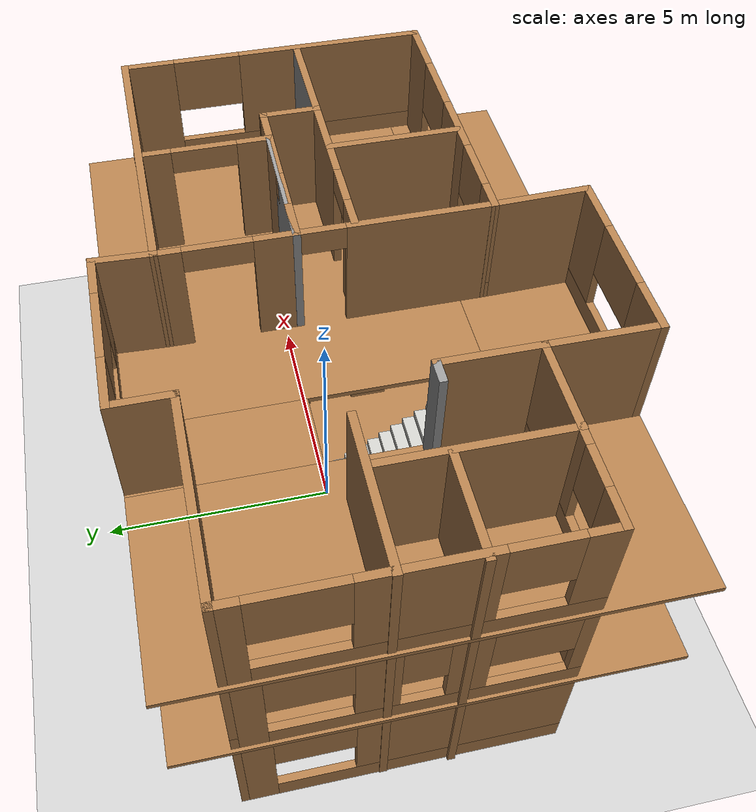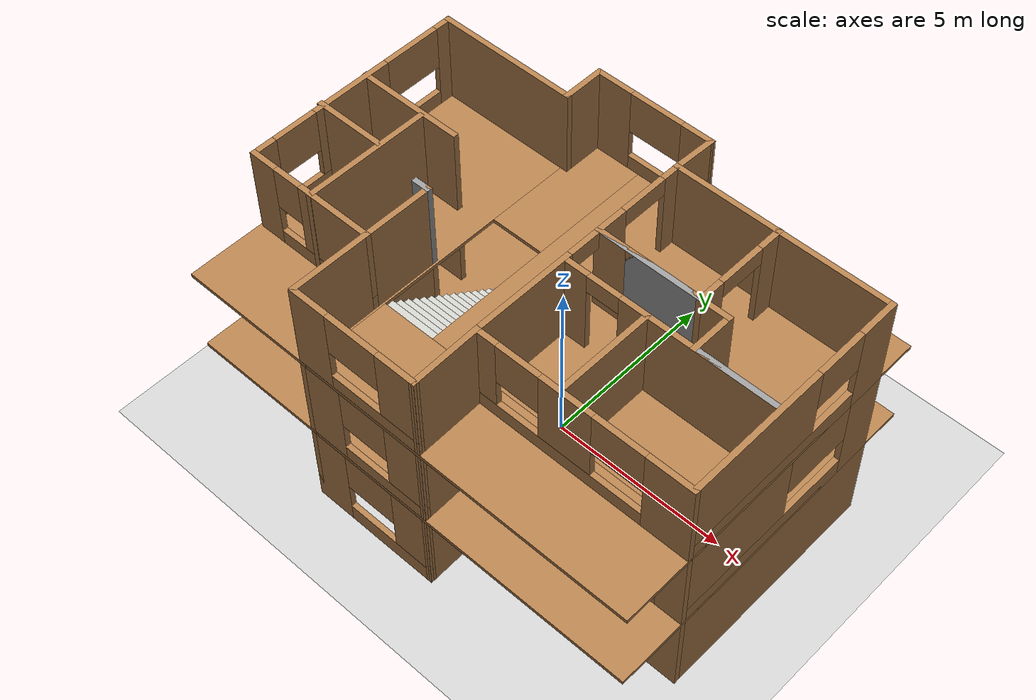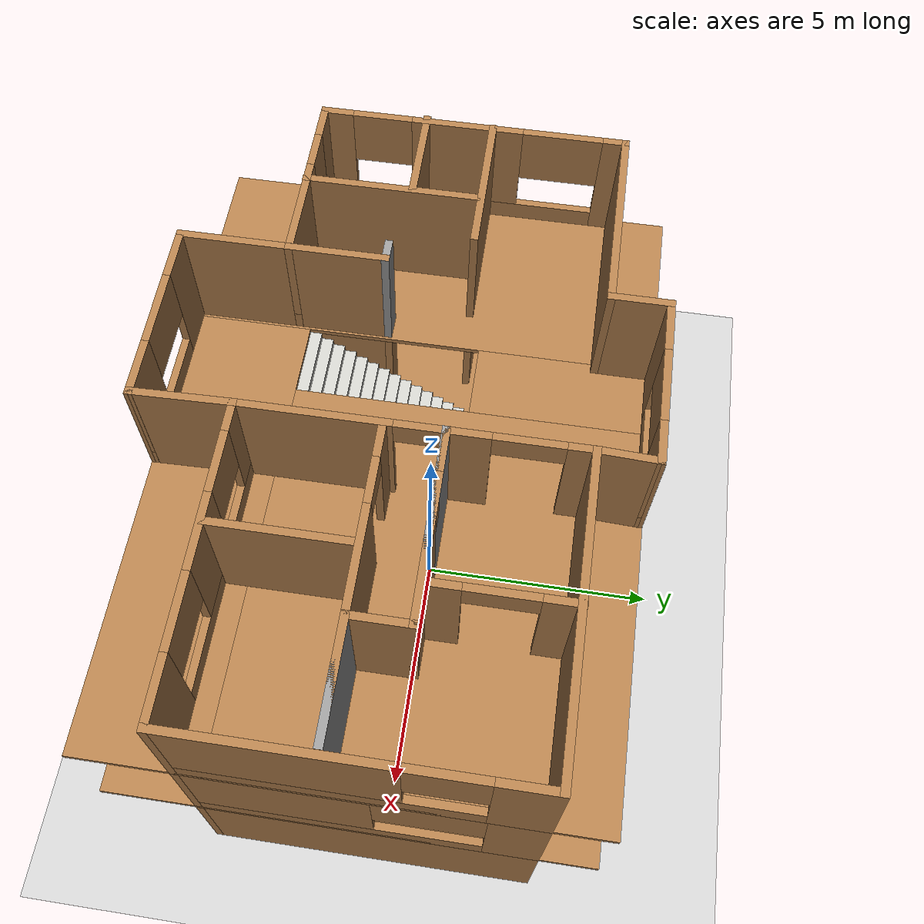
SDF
<sdf version="1.7">
 <world name="default">
  <light name="sun" type="directional">
   <pose>0 0 10 0 -0 0</pose>
   <diffuse>0.8 0.8 0.8 1</diffuse>
   <specular>0.2 0.2 0.2 1</specular>
   <attenuation>
    <range>1000</range>
    <constant>0.9</constant>
    <linear>0.01</linear>
    <quadratic>0.001</quadratic>
   </attenuation>
   <direction>-0.5 0.1 -0.9</direction>
   <spot><inner_angle>0</inner_angle><outer_angle>0</outer_angle><falloff>0</falloff></spot>
  </light>
  <model name="ground_plane">
   <static>1</static>
   <link name="link">
    <collision name="collision">
     <geometry><plane><normal>0 0 1</normal><size>100 100</size></plane></geometry>
     <surface>
      <contact><collide_bitmask>65535</collide_bitmask></contact>
      <friction><ode><mu>100</mu><mu2>50</mu2></ode></friction>
     </surface>
    </collision>
    <visual name="visual">
     <cast_shadows>0</cast_shadows>
     <geometry><plane><normal>0 0 1</normal><size>100 100</size></plane></geometry>
     <material>
      <script><uri>file://media/materials/scripts/gazebo.material</uri><name>Gazebo/Grey</name></script>
     </material>
    </visual>
   </link>
  </model>
  <gravity>0 0 -9.8</gravity>
  <magnetic_field>6e-06 2.3e-05 -4.2e-05</magnetic_field>
  <atmosphere type="adiabatic"/>
  <physics type="ode">
   <max_step_size>0.001</max_step_size>
   <real_time_factor>1</real_time_factor>
   <real_time_update_rate>1000</real_time_update_rate>
  </physics>
  <scene><ambient>0.4 0.4 0.4 1</ambient><background>0.7 0.7 0.7 1</background><shadows>1</shadows></scene>
  <spherical_coordinates>
   <surface_model>EARTH_WGS84</surface_model>
   <latitude_deg>0</latitude_deg>
   <longitude_deg>0</longitude_deg>
   <elevation>0</elevation>
   <heading_deg>0</heading_deg>
  </spherical_coordinates>
  <model name="three_level_house">
   <pose>0.012851 -0.612237 0 0 -0 0</pose>
   <link name="Floor_1">
    <pose>-0 0 2.5 0 -0 0</pose>
    <visual name="Floor_1_Visual_0">
     <pose>-4.68874 0 0.05 0 -0 0</pose>
     <geometry><box><size>3.84141 9.45494 0.1</size></box></geometry>
     <material>
      <script><uri>file://media/materials/scripts/gazebo.material</uri><name>Gazebo/Wood</name></script>
      <ambient>1 1 1 1</ambient>
     </material>
     <meta><layer>1</layer></meta>
    </visual>
    <collision name="Floor_1_Collision_0">
     <geometry><box><size>3.84141 9.45494 0.1</size></box></geometry>
     <pose>-4.68874 0 0.05 0 -0 0</pose>
    </collision>
    <visual name="Floor_1_Visual_1">
     <pose>1.9207 -3.52351 0.05 0 -0 0</pose>
     <geometry><box><size>9.37748 2.40791 0.1</size></box></geometry>
     <material>
      <script><uri>file://media/materials/scripts/gazebo.material</uri><name>Gazebo/Wood</name></script>
      <ambient>1 1 1 1</ambient>
     </material>
     <meta><layer>1</layer></meta>
    </visual>
    <collision name="Floor_1_Collision_1">
     <geometry><box><size>9.37748 2.40791 0.1</size></box></geometry>
     <pose>1.9207 -3.52351 0.05 0 -0 0</pose>
    </collision>
    <visual name="Floor_1_Visual_2">
     <pose>2.68227 1.20396 0.05 0 -0 0</pose>
     <geometry><box><size>7.85435 7.04702 0.1</size></box></geometry>
     <material>
      <script><uri>file://media/materials/scripts/gazebo.material</uri><name>Gazebo/Wood</name></script>
      <ambient>1 1 1 1</ambient>
     </material>
     <meta><layer>1</layer></meta>
    </visual>
    <collision name="Floor_1_Collision_2">
     <geometry><box><size>7.85435 7.04702 0.1</size></box></geometry>
     <pose>2.68227 1.20396 0.05 0 -0 0</pose>
    </collision>
    <visual name="Floor_1_Visual_3">
     <pose>-2.00647 2.95396 0.05 0 -0 0</pose>
     <geometry><box><size>1.52313 3.54703 0.1</size></box></geometry>
     <material>
      <script><uri>file://media/materials/scripts/gazebo.material</uri><name>Gazebo/Wood</name></script>
      <ambient>1 1 1 1</ambient>
     </material>
     <meta><layer>1</layer></meta>
    </visual>
    <collision name="Floor_1_Collision_3">
     <geometry><box><size>1.52313 3.54703 0.1</size></box></geometry>
     <pose>-2.00647 2.95396 0.05 0 -0 0</pose>
    </collision>
   </link>
   <link name="Floor_3">
    <pose>-0 0 5 0 -0 0</pose>
    <visual name="Floor_3_Visual_0">
     <pose>-4.67718 0 0.05 0 -0 0</pose>
     <geometry><box><size>3.86454 9.45494 0.1</size></box></geometry>
     <material>
      <script><uri>file://media/materials/scripts/gazebo.material</uri><name>Gazebo/Wood</name></script>
      <ambient>1 1 1 1</ambient>
     </material>
     <meta><layer>2</layer></meta>
    </visual>
    <collision name="Floor_3_Collision_0">
     <geometry><box><size>3.86454 9.45494 0.1</size></box></geometry>
     <pose>-4.67718 0 0.05 0 -0 0</pose>
    </collision>
    <visual name="Floor_3_Visual_1">
     <pose>1.93227 -3.52351 0.05 0 -0 0</pose>
     <geometry><box><size>9.35435 2.40791 0.1</size></box></geometry>
     <material>
      <script><uri>file://media/materials/scripts/gazebo.material</uri><name>Gazebo/Wood</name></script>
      <ambient>1 1 1 1</ambient>
     </material>
     <meta><layer>2</layer></meta>
    </visual>
    <collision name="Floor_3_Collision_1">
     <geometry><box><size>9.35435 2.40791 0.1</size></box></geometry>
     <pose>1.93227 -3.52351 0.05 0 -0 0</pose>
    </collision>
    <visual name="Floor_3_Visual_2">
     <pose>2.68227 1.20396 0.05 0 -0 0</pose>
     <geometry><box><size>7.85435 7.04702 0.1</size></box></geometry>
     <material>
      <script><uri>file://media/materials/scripts/gazebo.material</uri><name>Gazebo/Wood</name></script>
      <ambient>1 1 1 1</ambient>
     </material>
     <meta><layer>2</layer></meta>
    </visual>
    <collision name="Floor_3_Collision_2">
     <geometry><box><size>7.85435 7.04702 0.1</size></box></geometry>
     <pose>2.68227 1.20396 0.05 0 -0 0</pose>
    </collision>
    <visual name="Floor_3_Visual_3">
     <pose>-1.99491 2.95396 0.05 0 -0 0</pose>
     <geometry><box><size>1.5 3.54703 0.1</size></box></geometry>
     <material>
      <script><uri>file://media/materials/scripts/gazebo.material</uri><name>Gazebo/Wood</name></script>
      <ambient>1 1 1 1</ambient>
     </material>
     <meta><layer>2</layer></meta>
    </visual>
    <collision name="Floor_3_Collision_3">
     <geometry><box><size>1.5 3.54703 0.1</size></box></geometry>
     <pose>-1.99491 2.95396 0.05 0 -0 0</pose>
    </collision>
   </link>
   <link name="Stairs_0">
    <visual name="Stairs_0_Visual_0">
     <pose>-2.00647 1.06378 0.083333 0 -0 0</pose>
     <geometry><box><size>1.52313 0.233333 0.166667</size></box></geometry>
     <material>
      <script><uri>file://media/materials/scripts/gazebo.material</uri><name>Gazebo/CeilingTiled</name></script>
      <ambient>0.435294 0.796078 0.67451 1</ambient>
     </material>
     <meta><layer>0</layer></meta>
    </visual>
    <collision name="Stairs_0_Collision_0">
     <geometry><box><size>1.52313 0.233333 0.166667</size></box></geometry>
     <pose>-2.00647 1.06378 0.083333 0 -0 0</pose>
    </collision>
    <visual name="Stairs_0_Visual_1">
     <pose>-2.00647 0.830444 0.25 0 -0 0</pose>
     <geometry><box><size>1.52313 0.233333 0.166667</size></box></geometry>
     <material>
      <script><uri>file://media/materials/scripts/gazebo.material</uri><name>Gazebo/CeilingTiled</name></script>
      <ambient>0.435294 0.796078 0.67451 1</ambient>
     </material>
     <meta><layer>0</layer></meta>
    </visual>
    <collision name="Stairs_0_Collision_1">
     <geometry><box><size>1.52313 0.233333 0.166667</size></box></geometry>
     <pose>-2.00647 0.830444 0.25 0 -0 0</pose>
    </collision>
    <visual name="Stairs_0_Visual_2">
     <pose>-2.00647 0.59711 0.416667 0 -0 0</pose>
     <geometry><box><size>1.52313 0.233333 0.166667</size></box></geometry>
     <material>
      <script><uri>file://media/materials/scripts/gazebo.material</uri><name>Gazebo/CeilingTiled</name></script>
      <ambient>0.435294 0.796078 0.67451 1</ambient>
     </material>
     <meta><layer>0</layer></meta>
    </visual>
    <collision name="Stairs_0_Collision_2">
     <geometry><box><size>1.52313 0.233333 0.166667</size></box></geometry>
     <pose>-2.00647 0.59711 0.416667 0 -0 0</pose>
    </collision>
    <visual name="Stairs_0_Visual_3">
     <pose>-2.00647 0.363777 0.583333 0 -0 0</pose>
     <geometry><box><size>1.52313 0.233333 0.166667</size></box></geometry>
     <material>
      <script><uri>file://media/materials/scripts/gazebo.material</uri><name>Gazebo/CeilingTiled</name></script>
      <ambient>0.435294 0.796078 0.67451 1</ambient>
     </material>
     <meta><layer>0</layer></meta>
    </visual>
    <collision name="Stairs_0_Collision_3">
     <geometry><box><size>1.52313 0.233333 0.166667</size></box></geometry>
     <pose>-2.00647 0.363777 0.583333 0 -0 0</pose>
    </collision>
    <visual name="Stairs_0_Visual_4">
     <pose>-2.00647 0.130444 0.75 0 -0 0</pose>
     <geometry><box><size>1.52313 0.233333 0.166667</size></box></geometry>
     <material>
      <script><uri>file://media/materials/scripts/gazebo.material</uri><name>Gazebo/CeilingTiled</name></script>
      <ambient>0.435294 0.796078 0.67451 1</ambient>
     </material>
     <meta><layer>0</layer></meta>
    </visual>
    <collision name="Stairs_0_Collision_4">
     <geometry><box><size>1.52313 0.233333 0.166667</size></box></geometry>
     <pose>-2.00647 0.130444 0.75 0 -0 0</pose>
    </collision>
    <visual name="Stairs_0_Visual_5">
     <pose>-2.00647 -0.10289 0.916667 0 -0 0</pose>
     <geometry><box><size>1.52313 0.233333 0.166667</size></box></geometry>
     <material>
      <script><uri>file://media/materials/scripts/gazebo.material</uri><name>Gazebo/CeilingTiled</name></script>
      <ambient>0.435294 0.796078 0.67451 1</ambient>
     </material>
     <meta><layer>0</layer></meta>
    </visual>
    <collision name="Stairs_0_Collision_5">
     <geometry><box><size>1.52313 0.233333 0.166667</size></box></geometry>
     <pose>-2.00647 -0.10289 0.916667 0 -0 0</pose>
    </collision>
    <visual name="Stairs_0_Visual_6">
     <pose>-2.00647 -0.336223 1.08333 0 -0 0</pose>
     <geometry><box><size>1.52313 0.233333 0.166667</size></box></geometry>
     <material>
      <script><uri>file://media/materials/scripts/gazebo.material</uri><name>Gazebo/CeilingTiled</name></script>
      <ambient>0.435294 0.796078 0.67451 1</ambient>
     </material>
     <meta><layer>0</layer></meta>
    </visual>
    <collision name="Stairs_0_Collision_6">
     <geometry><box><size>1.52313 0.233333 0.166667</size></box></geometry>
     <pose>-2.00647 -0.336223 1.08333 0 -0 0</pose>
    </collision>
    <visual name="Stairs_0_Visual_7">
     <pose>-2.00647 -0.569556 1.25 0 -0 0</pose>
     <geometry><box><size>1.52313 0.233333 0.166667</size></box></geometry>
     <material>
      <script><uri>file://media/materials/scripts/gazebo.material</uri><name>Gazebo/CeilingTiled</name></script>
      <ambient>0.435294 0.796078 0.67451 1</ambient>
     </material>
     <meta><layer>0</layer></meta>
    </visual>
    <collision name="Stairs_0_Collision_7">
     <geometry><box><size>1.52313 0.233333 0.166667</size></box></geometry>
     <pose>-2.00647 -0.569556 1.25 0 -0 0</pose>
    </collision>
    <visual name="Stairs_0_Visual_8">
     <pose>-2.00647 -0.80289 1.41667 0 -0 0</pose>
     <geometry><box><size>1.52313 0.233333 0.166667</size></box></geometry>
     <material>
      <script><uri>file://media/materials/scripts/gazebo.material</uri><name>Gazebo/CeilingTiled</name></script>
      <ambient>0.435294 0.796078 0.67451 1</ambient>
     </material>
     <meta><layer>0</layer></meta>
    </visual>
    <collision name="Stairs_0_Collision_8">
     <geometry><box><size>1.52313 0.233333 0.166667</size></box></geometry>
     <pose>-2.00647 -0.80289 1.41667 0 -0 0</pose>
    </collision>
    <visual name="Stairs_0_Visual_9">
     <pose>-2.00647 -1.03622 1.58333 0 -0 0</pose>
     <geometry><box><size>1.52313 0.233333 0.166667</size></box></geometry>
     <material>
      <script><uri>file://media/materials/scripts/gazebo.material</uri><name>Gazebo/CeilingTiled</name></script>
      <ambient>0.435294 0.796078 0.67451 1</ambient>
     </material>
     <meta><layer>0</layer></meta>
    </visual>
    <collision name="Stairs_0_Collision_9">
     <geometry><box><size>1.52313 0.233333 0.166667</size></box></geometry>
     <pose>-2.00647 -1.03622 1.58333 0 -0 0</pose>
    </collision>
    <visual name="Stairs_0_Visual_10">
     <pose>-2.00647 -1.26956 1.75 0 -0 0</pose>
     <geometry><box><size>1.52313 0.233333 0.166667</size></box></geometry>
     <material>
      <script><uri>file://media/materials/scripts/gazebo.material</uri><name>Gazebo/CeilingTiled</name></script>
      <ambient>0.435294 0.796078 0.67451 1</ambient>
     </material>
     <meta><layer>0</layer></meta>
    </visual>
    <collision name="Stairs_0_Collision_10">
     <geometry><box><size>1.52313 0.233333 0.166667</size></box></geometry>
     <pose>-2.00647 -1.26956 1.75 0 -0 0</pose>
    </collision>
    <visual name="Stairs_0_Visual_11">
     <pose>-2.00647 -1.50289 1.91667 0 -0 0</pose>
     <geometry><box><size>1.52313 0.233333 0.166667</size></box></geometry>
     <material>
      <script><uri>file://media/materials/scripts/gazebo.material</uri><name>Gazebo/CeilingTiled</name></script>
      <ambient>0.435294 0.796078 0.67451 1</ambient>
     </material>
     <meta><layer>0</layer></meta>
    </visual>
    <collision name="Stairs_0_Collision_11">
     <geometry><box><size>1.52313 0.233333 0.166667</size></box></geometry>
     <pose>-2.00647 -1.50289 1.91667 0 -0 0</pose>
    </collision>
    <visual name="Stairs_0_Visual_12">
     <pose>-2.00647 -1.73622 2.08333 0 -0 0</pose>
     <geometry><box><size>1.52313 0.233333 0.166667</size></box></geometry>
     <material>
      <script><uri>file://media/materials/scripts/gazebo.material</uri><name>Gazebo/CeilingTiled</name></script>
      <ambient>0.435294 0.796078 0.67451 1</ambient>
     </material>
     <meta><layer>0</layer></meta>
    </visual>
    <collision name="Stairs_0_Collision_12">
     <geometry><box><size>1.52313 0.233333 0.166667</size></box></geometry>
     <pose>-2.00647 -1.73622 2.08333 0 -0 0</pose>
    </collision>
    <visual name="Stairs_0_Visual_13">
     <pose>-2.00647 -1.96956 2.25 0 -0 0</pose>
     <geometry><box><size>1.52313 0.233333 0.166667</size></box></geometry>
     <material>
      <script><uri>file://media/materials/scripts/gazebo.material</uri><name>Gazebo/CeilingTiled</name></script>
      <ambient>0.435294 0.796078 0.67451 1</ambient>
     </material>
     <meta><layer>0</layer></meta>
    </visual>
    <collision name="Stairs_0_Collision_13">
     <geometry><box><size>1.52313 0.233333 0.166667</size></box></geometry>
     <pose>-2.00647 -1.96956 2.25 0 -0 0</pose>
    </collision>
    <visual name="Stairs_0_Visual_14">
     <pose>-2.00647 -2.20289 2.41667 0 -0 0</pose>
     <geometry><box><size>1.52313 0.233333 0.166667</size></box></geometry>
     <material>
      <script><uri>file://media/materials/scripts/gazebo.material</uri><name>Gazebo/CeilingTiled</name></script>
      <ambient>0.435294 0.796078 0.67451 1</ambient>
     </material>
     <meta><layer>0</layer></meta>
    </visual>
    <collision name="Stairs_0_Collision_14">
     <geometry><box><size>1.52313 0.233333 0.166667</size></box></geometry>
     <pose>-2.00647 -2.20289 2.41667 0 -0 0</pose>
    </collision>
   </link>
   <link name="Stairs_1">
    <visual name="Stairs_1_Visual_0">
     <pose>-1.99491 1.06378 2.58333 0 -0 0</pose>
     <geometry><box><size>1.5 0.233333 0.166667</size></box></geometry>
     <material>
      <script><uri>file://media/materials/scripts/gazebo.material</uri><name>Gazebo/CeilingTiled</name></script>
      <ambient>0.435294 0.796078 0.67451 1</ambient>
     </material>
     <meta><layer>1</layer></meta>
    </visual>
    <collision name="Stairs_1_Collision_0">
     <geometry><box><size>1.5 0.233333 0.166667</size></box></geometry>
     <pose>-1.99491 1.06378 2.58333 0 -0 0</pose>
    </collision>
    <visual name="Stairs_1_Visual_1">
     <pose>-1.99491 0.830444 2.75 0 -0 0</pose>
     <geometry><box><size>1.5 0.233333 0.166667</size></box></geometry>
     <material>
      <script><uri>file://media/materials/scripts/gazebo.material</uri><name>Gazebo/CeilingTiled</name></script>
      <ambient>0.435294 0.796078 0.67451 1</ambient>
     </material>
     <meta><layer>1</layer></meta>
    </visual>
    <collision name="Stairs_1_Collision_1">
     <geometry><box><size>1.5 0.233333 0.166667</size></box></geometry>
     <pose>-1.99491 0.830444 2.75 0 -0 0</pose>
    </collision>
    <visual name="Stairs_1_Visual_2">
     <pose>-1.99491 0.59711 2.91667 0 -0 0</pose>
     <geometry><box><size>1.5 0.233333 0.166667</size></box></geometry>
     <material>
      <script><uri>file://media/materials/scripts/gazebo.material</uri><name>Gazebo/CeilingTiled</name></script>
      <ambient>0.435294 0.796078 0.67451 1</ambient>
     </material>
     <meta><layer>1</layer></meta>
    </visual>
    <collision name="Stairs_1_Collision_2">
     <geometry><box><size>1.5 0.233333 0.166667</size></box></geometry>
     <pose>-1.99491 0.59711 2.91667 0 -0 0</pose>
    </collision>
    <visual name="Stairs_1_Visual_3">
     <pose>-1.99491 0.363777 3.08333 0 -0 0</pose>
     <geometry><box><size>1.5 0.233333 0.166667</size></box></geometry>
     <material>
      <script><uri>file://media/materials/scripts/gazebo.material</uri><name>Gazebo/CeilingTiled</name></script>
      <ambient>0.435294 0.796078 0.67451 1</ambient>
     </material>
     <meta><layer>1</layer></meta>
    </visual>
    <collision name="Stairs_1_Collision_3">
     <geometry><box><size>1.5 0.233333 0.166667</size></box></geometry>
     <pose>-1.99491 0.363777 3.08333 0 -0 0</pose>
    </collision>
    <visual name="Stairs_1_Visual_4">
     <pose>-1.99491 0.130444 3.25 0 -0 0</pose>
     <geometry><box><size>1.5 0.233333 0.166667</size></box></geometry>
     <material>
      <script><uri>file://media/materials/scripts/gazebo.material</uri><name>Gazebo/CeilingTiled</name></script>
      <ambient>0.435294 0.796078 0.67451 1</ambient>
     </material>
     <meta><layer>1</layer></meta>
    </visual>
    <collision name="Stairs_1_Collision_4">
     <geometry><box><size>1.5 0.233333 0.166667</size></box></geometry>
     <pose>-1.99491 0.130444 3.25 0 -0 0</pose>
    </collision>
    <visual name="Stairs_1_Visual_5">
     <pose>-1.99491 -0.10289 3.41667 0 -0 0</pose>
     <geometry><box><size>1.5 0.233333 0.166667</size></box></geometry>
     <material>
      <script><uri>file://media/materials/scripts/gazebo.material</uri><name>Gazebo/CeilingTiled</name></script>
      <ambient>0.435294 0.796078 0.67451 1</ambient>
     </material>
     <meta><layer>1</layer></meta>
    </visual>
    <collision name="Stairs_1_Collision_5">
     <geometry><box><size>1.5 0.233333 0.166667</size></box></geometry>
     <pose>-1.99491 -0.10289 3.41667 0 -0 0</pose>
    </collision>
    <visual name="Stairs_1_Visual_6">
     <pose>-1.99491 -0.336223 3.58333 0 -0 0</pose>
     <geometry><box><size>1.5 0.233333 0.166667</size></box></geometry>
     <material>
      <script><uri>file://media/materials/scripts/gazebo.material</uri><name>Gazebo/CeilingTiled</name></script>
      <ambient>0.435294 0.796078 0.67451 1</ambient>
     </material>
     <meta><layer>1</layer></meta>
    </visual>
    <collision name="Stairs_1_Collision_6">
     <geometry><box><size>1.5 0.233333 0.166667</size></box></geometry>
     <pose>-1.99491 -0.336223 3.58333 0 -0 0</pose>
    </collision>
    <visual name="Stairs_1_Visual_7">
     <pose>-1.99491 -0.569556 3.75 0 -0 0</pose>
     <geometry><box><size>1.5 0.233333 0.166667</size></box></geometry>
     <material>
      <script><uri>file://media/materials/scripts/gazebo.material</uri><name>Gazebo/CeilingTiled</name></script>
      <ambient>0.435294 0.796078 0.67451 1</ambient>
     </material>
     <meta><layer>1</layer></meta>
    </visual>
    <collision name="Stairs_1_Collision_7">
     <geometry><box><size>1.5 0.233333 0.166667</size></box></geometry>
     <pose>-1.99491 -0.569556 3.75 0 -0 0</pose>
    </collision>
    <visual name="Stairs_1_Visual_8">
     <pose>-1.99491 -0.80289 3.91667 0 -0 0</pose>
     <geometry><box><size>1.5 0.233333 0.166667</size></box></geometry>
     <material>
      <script><uri>file://media/materials/scripts/gazebo.material</uri><name>Gazebo/CeilingTiled</name></script>
      <ambient>0.435294 0.796078 0.67451 1</ambient>
     </material>
     <meta><layer>1</layer></meta>
    </visual>
    <collision name="Stairs_1_Collision_8">
     <geometry><box><size>1.5 0.233333 0.166667</size></box></geometry>
     <pose>-1.99491 -0.80289 3.91667 0 -0 0</pose>
    </collision>
    <visual name="Stairs_1_Visual_9">
     <pose>-1.99491 -1.03622 4.08333 0 -0 0</pose>
     <geometry><box><size>1.5 0.233333 0.166667</size></box></geometry>
     <material>
      <script><uri>file://media/materials/scripts/gazebo.material</uri><name>Gazebo/CeilingTiled</name></script>
      <ambient>0.435294 0.796078 0.67451 1</ambient>
     </material>
     <meta><layer>1</layer></meta>
    </visual>
    <collision name="Stairs_1_Collision_9">
     <geometry><box><size>1.5 0.233333 0.166667</size></box></geometry>
     <pose>-1.99491 -1.03622 4.08333 0 -0 0</pose>
    </collision>
    <visual name="Stairs_1_Visual_10">
     <pose>-1.99491 -1.26956 4.25 0 -0 0</pose>
     <geometry><box><size>1.5 0.233333 0.166667</size></box></geometry>
     <material>
      <script><uri>file://media/materials/scripts/gazebo.material</uri><name>Gazebo/CeilingTiled</name></script>
      <ambient>0.435294 0.796078 0.67451 1</ambient>
     </material>
     <meta><layer>1</layer></meta>
    </visual>
    <collision name="Stairs_1_Collision_10">
     <geometry><box><size>1.5 0.233333 0.166667</size></box></geometry>
     <pose>-1.99491 -1.26956 4.25 0 -0 0</pose>
    </collision>
    <visual name="Stairs_1_Visual_11">
     <pose>-1.99491 -1.50289 4.41667 0 -0 0</pose>
     <geometry><box><size>1.5 0.233333 0.166667</size></box></geometry>
     <material>
      <script><uri>file://media/materials/scripts/gazebo.material</uri><name>Gazebo/CeilingTiled</name></script>
      <ambient>0.435294 0.796078 0.67451 1</ambient>
     </material>
     <meta><layer>1</layer></meta>
    </visual>
    <collision name="Stairs_1_Collision_11">
     <geometry><box><size>1.5 0.233333 0.166667</size></box></geometry>
     <pose>-1.99491 -1.50289 4.41667 0 -0 0</pose>
    </collision>
    <visual name="Stairs_1_Visual_12">
     <pose>-1.99491 -1.73622 4.58333 0 -0 0</pose>
     <geometry><box><size>1.5 0.233333 0.166667</size></box></geometry>
     <material>
      <script><uri>file://media/materials/scripts/gazebo.material</uri><name>Gazebo/CeilingTiled</name></script>
      <ambient>0.435294 0.796078 0.67451 1</ambient>
     </material>
     <meta><layer>1</layer></meta>
    </visual>
    <collision name="Stairs_1_Collision_12">
     <geometry><box><size>1.5 0.233333 0.166667</size></box></geometry>
     <pose>-1.99491 -1.73622 4.58333 0 -0 0</pose>
    </collision>
    <visual name="Stairs_1_Visual_13">
     <pose>-1.99491 -1.96956 4.75 0 -0 0</pose>
     <geometry><box><size>1.5 0.233333 0.166667</size></box></geometry>
     <material>
      <script><uri>file://media/materials/scripts/gazebo.material</uri><name>Gazebo/CeilingTiled</name></script>
      <ambient>0.435294 0.796078 0.67451 1</ambient>
     </material>
     <meta><layer>1</layer></meta>
    </visual>
    <collision name="Stairs_1_Collision_13">
     <geometry><box><size>1.5 0.233333 0.166667</size></box></geometry>
     <pose>-1.99491 -1.96956 4.75 0 -0 0</pose>
    </collision>
    <visual name="Stairs_1_Visual_14">
     <pose>-1.99491 -2.20289 4.91667 0 -0 0</pose>
     <geometry><box><size>1.5 0.233333 0.166667</size></box></geometry>
     <material>
      <script><uri>file://media/materials/scripts/gazebo.material</uri><name>Gazebo/CeilingTiled</name></script>
      <ambient>0.435294 0.796078 0.67451 1</ambient>
     </material>
     <meta><layer>1</layer></meta>
    </visual>
    <collision name="Stairs_1_Collision_14">
     <geometry><box><size>1.5 0.233333 0.166667</size></box></geometry>
     <pose>-1.99491 -2.20289 4.91667 0 -0 0</pose>
    </collision>
   </link>
   <link name="Wall_0">
    <pose>-0.944295 4.64938 0 0 -0 0</pose>
    <visual name="Wall_0_Visual_0">
     <pose>-1.29181 0 1.25 0 -0 0</pose>
     <geometry><box><size>0.916373 0.15 2.5</size></box></geometry>
     <material>
      <script><uri>file://media/materials/scripts/gazebo.material</uri><name>Gazebo/Wood</name></script>
      <ambient>1 1 1 1</ambient>
     </material>
     <meta><layer>0</layer></meta>
    </visual>
    <collision name="Wall_0_Collision_0">
     <geometry><box><size>0.916373 0.15 2.5</size></box></geometry>
     <pose>-1.29181 0 1.25 0 -0 0</pose>
    </collision>
    <visual name="Wall_0_Visual_1">
     <pose>0.458187 0 0.25 0 -0 0</pose>
     <geometry><box><size>2.58363 0.15 0.5</size></box></geometry>
     <material>
      <script><uri>file://media/materials/scripts/gazebo.material</uri><name>Gazebo/Wood</name></script>
      <ambient>1 1 1 1</ambient>
     </material>
     <meta><layer>0</layer></meta>
    </visual>
    <collision name="Wall_0_Collision_1">
     <geometry><box><size>2.58363 0.15 0.5</size></box></geometry>
     <pose>0.458187 0 0.25 0 -0 0</pose>
    </collision>
    <visual name="Wall_0_Visual_2">
     <pose>1.30819 0 1.5 0 -0 0</pose>
     <geometry><box><size>0.883627 0.15 2</size></box></geometry>
     <material>
      <script><uri>file://media/materials/scripts/gazebo.material</uri><name>Gazebo/Wood</name></script>
      <ambient>1 1 1 1</ambient>
     </material>
     <meta><layer>0</layer></meta>
    </visual>
    <collision name="Wall_0_Collision_2">
     <geometry><box><size>0.883627 0.15 2</size></box></geometry>
     <pose>1.30819 0 1.5 0 -0 0</pose>
    </collision>
    <visual name="Wall_0_Visual_3">
     <pose>0.016373 0 1.9 0 -0 0</pose>
     <geometry><box><size>1.7 0.15 1.2</size></box></geometry>
     <material>
      <script><uri>file://media/materials/scripts/gazebo.material</uri><name>Gazebo/Wood</name></script>
      <ambient>1 1 1 1</ambient>
     </material>
     <meta><layer>0</layer></meta>
    </visual>
    <collision name="Wall_0_Collision_3">
     <geometry><box><size>1.7 0.15 1.2</size></box></geometry>
     <pose>0.016373 0 1.9 0 -0 0</pose>
    </collision>
   </link>
   <link name="Wall_1">
    <collision name="Wall_1_Collision">
     <geometry><box><size>1.25 0.15 2.5</size></box></geometry>
     <pose>0 0 1.25 0 -0 0</pose>
    </collision>
    <visual name="Wall_1_Visual">
     <pose>0 0 1.25 0 -0 0</pose>
     <geometry><box><size>1.25 0.15 2.5</size></box></geometry>
     <material>
      <script><uri>file://media/materials/scripts/gazebo.material</uri><name>Gazebo/Wood</name></script>
      <ambient>1 1 1 1</ambient>
     </material>
     <meta><layer>0</layer></meta>
    </visual>
    <pose>0.707575 4.09938 0 0 -0 -1.61283</pose>
   </link>
   <link name="Wall_10">
    <pose>0.684444 0.374383 0 0 -0 1.5708</pose>
    <visual name="Wall_10_Visual_0">
     <pose>-1.89481 0 1.25 0 -0 0</pose>
     <geometry><box><size>2.71039 0.15 2.5</size></box></geometry>
     <material>
      <script><uri>file://media/materials/scripts/gazebo.material</uri><name>Gazebo/Wood</name></script>
      <ambient>1 1 1 1</ambient>
     </material>
     <meta><layer>0</layer></meta>
    </visual>
    <collision name="Wall_10_Collision_0">
     <geometry><box><size>2.71039 0.15 2.5</size></box></geometry>
     <pose>-1.89481 0 1.25 0 -0 0</pose>
    </collision>
    <visual name="Wall_10_Visual_1">
     <pose>1.8052 0 1.25 0 -0 0</pose>
     <geometry><box><size>2.88961 0.15 2.5</size></box></geometry>
     <material>
      <script><uri>file://media/materials/scripts/gazebo.material</uri><name>Gazebo/Wood</name></script>
      <ambient>1 1 1 1</ambient>
     </material>
     <meta><layer>0</layer></meta>
    </visual>
    <collision name="Wall_10_Collision_1">
     <geometry><box><size>2.88961 0.15 2.5</size></box></geometry>
     <pose>1.8052 0 1.25 0 -0 0</pose>
    </collision>
    <visual name="Wall_10_Visual_2">
     <pose>-0.08961 0 2.25 0 -0 0</pose>
     <geometry><box><size>0.9 0.15 0.5</size></box></geometry>
     <material>
      <script><uri>file://media/materials/scripts/gazebo.material</uri><name>Gazebo/Wood</name></script>
      <ambient>1 1 1 1</ambient>
     </material>
     <meta><layer>0</layer></meta>
    </visual>
    <collision name="Wall_10_Collision_2">
     <geometry><box><size>0.9 0.15 0.5</size></box></geometry>
     <pose>-0.08961 0 2.25 0 -0 0</pose>
    </collision>
   </link>
   <link name="Wall_113">
    <pose>-0.944295 4.64938 5 0 -0 0</pose>
    <visual name="Wall_113_Visual_0">
     <pose>-1.1952 0 1.25 0 -0 0</pose>
     <geometry><box><size>1.1096 0.15 2.5</size></box></geometry>
     <material>
      <script><uri>file://media/materials/scripts/gazebo.material</uri><name>Gazebo/Wood</name></script>
      <ambient>1 1 1 1</ambient>
     </material>
     <meta><layer>2</layer></meta>
    </visual>
    <collision name="Wall_113_Collision_0">
     <geometry><box><size>1.1096 0.15 2.5</size></box></geometry>
     <pose>-1.1952 0 1.25 0 -0 0</pose>
    </collision>
    <visual name="Wall_113_Visual_1">
     <pose>0.554801 0 0.25 0 -0 0</pose>
     <geometry><box><size>2.3904 0.15 0.5</size></box></geometry>
     <material>
      <script><uri>file://media/materials/scripts/gazebo.material</uri><name>Gazebo/Wood</name></script>
      <ambient>1 1 1 1</ambient>
     </material>
     <meta><layer>2</layer></meta>
    </visual>
    <collision name="Wall_113_Collision_1">
     <geometry><box><size>2.3904 0.15 0.5</size></box></geometry>
     <pose>0.554801 0 0.25 0 -0 0</pose>
    </collision>
    <visual name="Wall_113_Visual_2">
     <pose>1.3048 0 1.5 0 -0 0</pose>
     <geometry><box><size>0.890397 0.15 2</size></box></geometry>
     <material>
      <script><uri>file://media/materials/scripts/gazebo.material</uri><name>Gazebo/Wood</name></script>
      <ambient>1 1 1 1</ambient>
     </material>
     <meta><layer>2</layer></meta>
    </visual>
    <collision name="Wall_113_Collision_2">
     <geometry><box><size>0.890397 0.15 2</size></box></geometry>
     <pose>1.3048 0 1.5 0 -0 0</pose>
    </collision>
    <visual name="Wall_113_Visual_3">
     <pose>0.109603 0 1.9 0 -0 0</pose>
     <geometry><box><size>1.5 0.15 1.2</size></box></geometry>
     <material>
      <script><uri>file://media/materials/scripts/gazebo.material</uri><name>Gazebo/Wood</name></script>
      <ambient>1 1 1 1</ambient>
     </material>
     <meta><layer>2</layer></meta>
    </visual>
    <collision name="Wall_113_Collision_3">
     <geometry><box><size>1.5 0.15 1.2</size></box></geometry>
     <pose>0.109603 0 1.9 0 -0 0</pose>
    </collision>
   </link>
   <link name="Wall_114">
    <collision name="Wall_114_Collision">
     <geometry><box><size>1.25097 0.15 2.5</size></box></geometry>
     <pose>0 0 1.25 0 -0 0</pose>
    </collision>
    <visual name="Wall_114_Visual">
     <pose>0 0 1.25 0 -0 0</pose>
     <geometry><box><size>1.25097 0.15 2.5</size></box></geometry>
     <material>
      <script><uri>file://media/materials/scripts/gazebo.material</uri><name>Gazebo/Wood</name></script>
      <ambient>1 1 1 1</ambient>
     </material>
     <meta><layer>2</layer></meta>
    </visual>
    <pose>0.707575 4.09938 5 0 -0 -1.61283</pose>
   </link>
   <link name="Wall_115">
    <collision name="Wall_115_Collision">
     <geometry><box><size>6 0.15 2.5</size></box></geometry>
     <pose>0 0 1.25 0 -0 0</pose>
    </collision>
    <visual name="Wall_115_Visual">
     <pose>0 0 1.25 0 -0 0</pose>
     <geometry><box><size>6 0.15 2.5</size></box></geometry>
     <material>
      <script><uri>file://media/materials/scripts/gazebo.material</uri><name>Gazebo/Wood</name></script>
      <ambient>1 1 1 1</ambient>
     </material>
     <meta><layer>2</layer></meta>
    </visual>
    <pose>3.60944 3.54938 5 0 -0 0</pose>
   </link>
   <link name="Wall_116">
    <pose>6.53444 0.374383 5 0 -0 -1.5708</pose>
    <visual name="Wall_116_Visual_0">
     <pose>-2.69584 0 1.25 0 -0 0</pose>
     <geometry><box><size>1.10832 0.15 2.5</size></box></geometry>
     <material>
      <script><uri>file://media/materials/scripts/gazebo.material</uri><name>Gazebo/Wood</name></script>
      <ambient>1 1 1 1</ambient>
     </material>
     <meta><layer>2</layer></meta>
    </visual>
    <collision name="Wall_116_Collision_0">
     <geometry><box><size>1.10832 0.15 2.5</size></box></geometry>
     <pose>-2.69584 0 1.25 0 -0 0</pose>
    </collision>
    <visual name="Wall_116_Visual_1">
     <pose>0.554159 0 0.25 0 -0 0</pose>
     <geometry><box><size>5.39168 0.15 0.5</size></box></geometry>
     <material>
      <script><uri>file://media/materials/scripts/gazebo.material</uri><name>Gazebo/Wood</name></script>
      <ambient>1 1 1 1</ambient>
     </material>
     <meta><layer>2</layer></meta>
    </visual>
    <collision name="Wall_116_Collision_1">
     <geometry><box><size>5.39168 0.15 0.5</size></box></geometry>
     <pose>0.554159 0 0.25 0 -0 0</pose>
    </collision>
    <visual name="Wall_116_Visual_2">
     <pose>1.25416 0 1.5 0 -0 0</pose>
     <geometry><box><size>3.99168 0.15 2</size></box></geometry>
     <material>
      <script><uri>file://media/materials/scripts/gazebo.material</uri><name>Gazebo/Wood</name></script>
      <ambient>1 1 1 1</ambient>
     </material>
     <meta><layer>2</layer></meta>
    </visual>
    <collision name="Wall_116_Collision_2">
     <geometry><box><size>3.99168 0.15 2</size></box></geometry>
     <pose>1.25416 0 1.5 0 -0 0</pose>
    </collision>
    <visual name="Wall_116_Visual_3">
     <pose>-1.44168 0 1.9 0 -0 0</pose>
     <geometry><box><size>1.4 0.15 1.2</size></box></geometry>
     <material>
      <script><uri>file://media/materials/scripts/gazebo.material</uri><name>Gazebo/Wood</name></script>
      <ambient>1 1 1 1</ambient>
     </material>
     <meta><layer>2</layer></meta>
    </visual>
    <collision name="Wall_116_Collision_3">
     <geometry><box><size>1.4 0.15 1.2</size></box></geometry>
     <pose>-1.44168 0 1.9 0 -0 0</pose>
    </collision>
   </link>
   <link name="Wall_117">
    <pose>3.60944 -2.80062 5 0 -0 3.14159</pose>
    <visual name="Wall_117_Visual_0">
     <pose>-2.35599 0 1.25 0 -0 0</pose>
     <geometry><box><size>1.28803 0.15 2.5</size></box></geometry>
     <material>
      <script><uri>file://media/materials/scripts/gazebo.material</uri><name>Gazebo/Wood</name></script>
      <ambient>1 1 1 1</ambient>
     </material>
     <meta><layer>2</layer></meta>
    </visual>
    <collision name="Wall_117_Collision_0">
     <geometry><box><size>1.28803 0.15 2.5</size></box></geometry>
     <pose>-2.35599 0 1.25 0 -0 0</pose>
    </collision>
    <visual name="Wall_117_Visual_1">
     <pose>0.644013 0 0.25 0 -0 0</pose>
     <geometry><box><size>4.71197 0.15 0.5</size></box></geometry>
     <material>
      <script><uri>file://media/materials/scripts/gazebo.material</uri><name>Gazebo/Wood</name></script>
      <ambient>1 1 1 1</ambient>
     </material>
     <meta><layer>2</layer></meta>
    </visual>
    <collision name="Wall_117_Collision_1">
     <geometry><box><size>4.71197 0.15 0.5</size></box></geometry>
     <pose>0.644013 0 0.25 0 -0 0</pose>
    </collision>
    <visual name="Wall_117_Visual_2">
     <pose>0.413516 0 1.5 0 -0 0</pose>
     <geometry><box><size>1.45098 0.15 2</size></box></geometry>
     <material>
      <script><uri>file://media/materials/scripts/gazebo.material</uri><name>Gazebo/Wood</name></script>
      <ambient>1 1 1 1</ambient>
     </material>
     <meta><layer>2</layer></meta>
    </visual>
    <collision name="Wall_117_Collision_2">
     <geometry><box><size>1.45098 0.15 2</size></box></geometry>
     <pose>0.413516 0 1.5 0 -0 0</pose>
    </collision>
    <visual name="Wall_117_Visual_3">
     <pose>2.6695 0 1.5 0 -0 0</pose>
     <geometry><box><size>0.660994 0.15 2</size></box></geometry>
     <material>
      <script><uri>file://media/materials/scripts/gazebo.material</uri><name>Gazebo/Wood</name></script>
      <ambient>1 1 1 1</ambient>
     </material>
     <meta><layer>2</layer></meta>
    </visual>
    <collision name="Wall_117_Collision_3">
     <geometry><box><size>0.660994 0.15 2</size></box></geometry>
     <pose>2.6695 0 1.5 0 -0 0</pose>
    </collision>
    <visual name="Wall_117_Visual_4">
     <pose>-1.01197 0 1.9 0 -0 0</pose>
     <geometry><box><size>1.4 0.15 1.2</size></box></geometry>
     <material>
      <script><uri>file://media/materials/scripts/gazebo.material</uri><name>Gazebo/Wood</name></script>
      <ambient>1 1 1 1</ambient>
     </material>
     <meta><layer>2</layer></meta>
    </visual>
    <collision name="Wall_117_Collision_4">
     <geometry><box><size>1.4 0.15 1.2</size></box></geometry>
     <pose>-1.01197 0 1.9 0 -0 0</pose>
    </collision>
    <visual name="Wall_117_Visual_5">
     <pose>1.73901 0 1.9 0 -0 0</pose>
     <geometry><box><size>1.2 0.15 1.2</size></box></geometry>
     <material>
      <script><uri>file://media/materials/scripts/gazebo.material</uri><name>Gazebo/Wood</name></script>
      <ambient>1 1 1 1</ambient>
     </material>
     <meta><layer>2</layer></meta>
    </visual>
    <collision name="Wall_117_Collision_5">
     <geometry><box><size>1.2 0.15 1.2</size></box></geometry>
     <pose>1.73901 0 1.9 0 -0 0</pose>
    </collision>
   </link>
   <link name="Wall_118">
    <pose>0.684444 0.374383 5 0 -0 1.5708</pose>
    <visual name="Wall_118_Visual_0">
     <pose>-1.79676 0 1.25 0 -0 0</pose>
     <geometry><box><size>2.90647 0.15 2.5</size></box></geometry>
     <material>
      <script><uri>file://media/materials/scripts/gazebo.material</uri><name>Gazebo/Wood</name></script>
      <ambient>1 1 1 1</ambient>
     </material>
     <meta><layer>2</layer></meta>
    </visual>
    <collision name="Wall_118_Collision_0">
     <geometry><box><size>2.90647 0.15 2.5</size></box></geometry>
     <pose>-1.79676 0 1.25 0 -0 0</pose>
    </collision>
    <visual name="Wall_118_Visual_1">
     <pose>0.96834 0 1.25 0 -0 0</pose>
     <geometry><box><size>0.823741 0.15 2.5</size></box></geometry>
     <material>
      <script><uri>file://media/materials/scripts/gazebo.material</uri><name>Gazebo/Wood</name></script>
      <ambient>1 1 1 1</ambient>
     </material>
     <meta><layer>2</layer></meta>
    </visual>
    <collision name="Wall_118_Collision_1">
     <geometry><box><size>0.823741 0.15 2.5</size></box></geometry>
     <pose>0.96834 0 1.25 0 -0 0</pose>
    </collision>
    <visual name="Wall_118_Visual_2">
     <pose>2.9651 0 1.25 0 -0 0</pose>
     <geometry><box><size>0.569789 0.15 2.5</size></box></geometry>
     <material>
      <script><uri>file://media/materials/scripts/gazebo.material</uri><name>Gazebo/Wood</name></script>
      <ambient>1 1 1 1</ambient>
     </material>
     <meta><layer>2</layer></meta>
    </visual>
    <collision name="Wall_118_Collision_2">
     <geometry><box><size>0.569789 0.15 2.5</size></box></geometry>
     <pose>2.9651 0 1.25 0 -0 0</pose>
    </collision>
    <visual name="Wall_118_Visual_3">
     <pose>0.106469 0 2.25 0 -0 0</pose>
     <geometry><box><size>0.9 0.15 0.5</size></box></geometry>
     <material>
      <script><uri>file://media/materials/scripts/gazebo.material</uri><name>Gazebo/Wood</name></script>
      <ambient>1 1 1 1</ambient>
     </material>
     <meta><layer>2</layer></meta>
    </visual>
    <collision name="Wall_118_Collision_3">
     <geometry><box><size>0.9 0.15 0.5</size></box></geometry>
     <pose>0.106469 0 2.25 0 -0 0</pose>
    </collision>
    <visual name="Wall_118_Visual_4">
     <pose>2.03021 0 2.25 0 -0 0</pose>
     <geometry><box><size>1.3 0.15 0.5</size></box></geometry>
     <material>
      <script><uri>file://media/materials/scripts/gazebo.material</uri><name>Gazebo/Wood</name></script>
      <ambient>1 1 1 1</ambient>
     </material>
     <meta><layer>2</layer></meta>
    </visual>
    <collision name="Wall_118_Collision_4">
     <geometry><box><size>1.3 0.15 0.5</size></box></geometry>
     <pose>2.03021 0 2.25 0 -0 0</pose>
    </collision>
   </link>
   <link name="Wall_119">
    <collision name="Wall_119_Collision">
     <geometry><box><size>1.25 0.15 2.5</size></box></geometry>
     <pose>0 0 1.25 0 -0 0</pose>
    </collision>
    <visual name="Wall_119_Visual">
     <pose>0 0 1.25 0 -0 0</pose>
     <geometry><box><size>1.25 0.15 2.5</size></box></geometry>
     <material>
      <script><uri>file://media/materials/scripts/gazebo.material</uri><name>Gazebo/Wood</name></script>
      <ambient>1 1 1 1</ambient>
     </material>
     <meta><layer>2</layer></meta>
    </visual>
    <pose>-2.6193 4.09938 5 0 -0 -1.5708</pose>
   </link>
   <link name="Wall_12">
    <collision name="Wall_12_Collision">
     <geometry><box><size>1.25 0.15 2.5</size></box></geometry>
     <pose>0 0 1.25 0 -0 0</pose>
    </collision>
    <visual name="Wall_12_Visual">
     <pose>0 0 1.25 0 -0 0</pose>
     <geometry><box><size>1.25 0.15 2.5</size></box></geometry>
     <material>
      <script><uri>file://media/materials/scripts/gazebo.material</uri><name>Gazebo/Wood</name></script>
      <ambient>1 1 1 1</ambient>
     </material>
     <meta><layer>0</layer></meta>
    </visual>
    <pose>-2.6193 4.09938 0 0 -0 -1.5708</pose>
   </link>
   <link name="Wall_120">
    <collision name="Wall_120_Collision">
     <geometry><box><size>4 0.15 2.5</size></box></geometry>
     <pose>0 0 1.25 0 -0 0</pose>
    </collision>
    <visual name="Wall_120_Visual">
     <pose>0 0 1.25 0 -0 0</pose>
     <geometry><box><size>4 0.15 2.5</size></box></geometry>
     <material>
      <script><uri>file://media/materials/scripts/gazebo.material</uri><name>Gazebo/Wood</name></script>
      <ambient>1 1 1 1</ambient>
     </material>
     <meta><layer>2</layer></meta>
    </visual>
    <pose>-4.54429 3.54938 5 0 -0 3.14159</pose>
   </link>
   <link name="Wall_121">
    <pose>-6.46929 0.499383 5 0 -0 -1.5708</pose>
    <visual name="Wall_121_Visual_0">
     <pose>-2.8616 0 1.25 0 -0 0</pose>
     <geometry><box><size>0.526794 0.15 2.5</size></box></geometry>
     <material>
      <script><uri>file://media/materials/scripts/gazebo.material</uri><name>Gazebo/Wood</name></script>
      <ambient>1 1 1 1</ambient>
     </material>
     <meta><layer>2</layer></meta>
    </visual>
    <collision name="Wall_121_Collision_0">
     <geometry><box><size>0.526794 0.15 2.5</size></box></geometry>
     <pose>-2.8616 0 1.25 0 -0 0</pose>
    </collision>
    <visual name="Wall_121_Visual_1">
     <pose>0.263397 0 0.25 0 -0 0</pose>
     <geometry><box><size>5.72321 0.15 0.5</size></box></geometry>
     <material>
      <script><uri>file://media/materials/scripts/gazebo.material</uri><name>Gazebo/Wood</name></script>
      <ambient>1 1 1 1</ambient>
     </material>
     <meta><layer>2</layer></meta>
    </visual>
    <collision name="Wall_121_Collision_1">
     <geometry><box><size>5.72321 0.15 0.5</size></box></geometry>
     <pose>0.263397 0 0.25 0 -0 0</pose>
    </collision>
    <visual name="Wall_121_Visual_2">
     <pose>0.130527 0 1.5 0 -0 0</pose>
     <geometry><box><size>2.25746 0.15 2</size></box></geometry>
     <material>
      <script><uri>file://media/materials/scripts/gazebo.material</uri><name>Gazebo/Wood</name></script>
      <ambient>1 1 1 1</ambient>
     </material>
     <meta><layer>2</layer></meta>
    </visual>
    <collision name="Wall_121_Collision_2">
     <geometry><box><size>2.25746 0.15 2</size></box></geometry>
     <pose>0.130527 0 1.5 0 -0 0</pose>
    </collision>
    <visual name="Wall_121_Visual_3">
     <pose>2.79213 0 1.5 0 -0 0</pose>
     <geometry><box><size>0.665741 0.15 2</size></box></geometry>
     <material>
      <script><uri>file://media/materials/scripts/gazebo.material</uri><name>Gazebo/Wood</name></script>
      <ambient>1 1 1 1</ambient>
     </material>
     <meta><layer>2</layer></meta>
    </visual>
    <collision name="Wall_121_Collision_3">
     <geometry><box><size>0.665741 0.15 2</size></box></geometry>
     <pose>2.79213 0 1.5 0 -0 0</pose>
    </collision>
    <visual name="Wall_121_Visual_4">
     <pose>-1.79821 0 1.9 0 -0 0</pose>
     <geometry><box><size>1.6 0.15 1.2</size></box></geometry>
     <material>
      <script><uri>file://media/materials/scripts/gazebo.material</uri><name>Gazebo/Wood</name></script>
      <ambient>1 1 1 1</ambient>
     </material>
     <meta><layer>2</layer></meta>
    </visual>
    <collision name="Wall_121_Collision_4">
     <geometry><box><size>1.6 0.15 1.2</size></box></geometry>
     <pose>-1.79821 0 1.9 0 -0 0</pose>
    </collision>
    <visual name="Wall_121_Visual_5">
     <pose>1.85926 0 1.9 0 -0 0</pose>
     <geometry><box><size>1.2 0.15 1.2</size></box></geometry>
     <material>
      <script><uri>file://media/materials/scripts/gazebo.material</uri><name>Gazebo/Wood</name></script>
      <ambient>1 1 1 1</ambient>
     </material>
     <meta><layer>2</layer></meta>
    </visual>
    <collision name="Wall_121_Collision_5">
     <geometry><box><size>1.2 0.15 1.2</size></box></geometry>
     <pose>1.85926 0 1.9 0 -0 0</pose>
    </collision>
   </link>
   <link name="Wall_122">
    <pose>-4.66929 -2.55062 5 0 -0 0</pose>
    <visual name="Wall_122_Visual_0">
     <pose>-1.48841 0 1.25 0 -0 0</pose>
     <geometry><box><size>0.773185 0.15 2.5</size></box></geometry>
     <material>
      <script><uri>file://media/materials/scripts/gazebo.material</uri><name>Gazebo/Wood</name></script>
      <ambient>1 1 1 1</ambient>
     </material>
     <meta><layer>2</layer></meta>
    </visual>
    <collision name="Wall_122_Collision_0">
     <geometry><box><size>0.773185 0.15 2.5</size></box></geometry>
     <pose>-1.48841 0 1.25 0 -0 0</pose>
    </collision>
    <visual name="Wall_122_Visual_1">
     <pose>0.386592 0 0.25 0 -0 0</pose>
     <geometry><box><size>2.97682 0.15 0.5</size></box></geometry>
     <material>
      <script><uri>file://media/materials/scripts/gazebo.material</uri><name>Gazebo/Wood</name></script>
      <ambient>1 1 1 1</ambient>
     </material>
     <meta><layer>2</layer></meta>
    </visual>
    <collision name="Wall_122_Collision_1">
     <geometry><box><size>2.97682 0.15 0.5</size></box></geometry>
     <pose>0.386592 0 0.25 0 -0 0</pose>
    </collision>
    <visual name="Wall_122_Visual_2">
     <pose>0.786592 0 1.5 0 -0 0</pose>
     <geometry><box><size>2.17681 0.15 2</size></box></geometry>
     <material>
      <script><uri>file://media/materials/scripts/gazebo.material</uri><name>Gazebo/Wood</name></script>
      <ambient>1 1 1 1</ambient>
     </material>
     <meta><layer>2</layer></meta>
    </visual>
    <collision name="Wall_122_Collision_2">
     <geometry><box><size>2.17681 0.15 2</size></box></geometry>
     <pose>0.786592 0 1.5 0 -0 0</pose>
    </collision>
    <visual name="Wall_122_Visual_3">
     <pose>-0.701815 0 1.9 0 -0 0</pose>
     <geometry><box><size>0.8 0.15 1.2</size></box></geometry>
     <material>
      <script><uri>file://media/materials/scripts/gazebo.material</uri><name>Gazebo/Wood</name></script>
      <ambient>1 1 1 1</ambient>
     </material>
     <meta><layer>2</layer></meta>
    </visual>
    <collision name="Wall_122_Collision_3">
     <geometry><box><size>0.8 0.15 1.2</size></box></geometry>
     <pose>-0.701815 0 1.9 0 -0 0</pose>
    </collision>
   </link>
   <link name="Wall_123">
    <collision name="Wall_123_Collision">
     <geometry><box><size>2 0.15 2.5</size></box></geometry>
     <pose>0 0 1.25 0 -0 0</pose>
    </collision>
    <visual name="Wall_123_Visual">
     <pose>0 0 1.25 0 -0 0</pose>
     <geometry><box><size>2 0.15 2.5</size></box></geometry>
     <material>
      <script><uri>file://media/materials/scripts/gazebo.material</uri><name>Gazebo/Wood</name></script>
      <ambient>1 1 1 1</ambient>
     </material>
     <meta><layer>2</layer></meta>
    </visual>
    <pose>-2.8693 -1.62562 5 0 -0 1.5708</pose>
   </link>
   <link name="Wall_124">
    <collision name="Wall_124_Collision">
     <geometry><box><size>0.5 0.15 2.5</size></box></geometry>
     <pose>0 0 1.25 0 -0 0</pose>
    </collision>
    <visual name="Wall_124_Visual">
     <pose>0 0 1.25 0 -0 0</pose>
     <geometry><box><size>0.5 0.15 2.5</size></box></geometry>
     <material>
      <script><uri>file://media/materials/scripts/gazebo.material</uri><name>Gazebo/Grey</name></script>
      <ambient>1 1 1 1</ambient>
     </material>
     <meta><layer>2</layer></meta>
    </visual>
    <pose>-3.04429 -0.700617 5 0 -0 3.14159</pose>
   </link>
   <link name="Wall_125">
    <collision name="Wall_125_Collision">
     <geometry><box><size>3 0.15 2.5</size></box></geometry>
     <pose>0 0 1.25 0 -0 0</pose>
    </collision>
    <visual name="Wall_125_Visual">
     <pose>0 0 1.25 0 -0 0</pose>
     <geometry><box><size>3 0.15 2.5</size></box></geometry>
     <material>
      <script><uri>file://media/materials/scripts/gazebo.material</uri><name>Gazebo/Wood</name></script>
      <ambient>1 1 1 1</ambient>
     </material>
     <meta><layer>2</layer></meta>
    </visual>
    <pose>-5.06058 0.88243 5 0 -0 0</pose>
   </link>
   <link name="Wall_126">
    <collision name="Wall_126_Collision">
     <geometry><box><size>3.5 0.15 2.5</size></box></geometry>
     <pose>0 0 1.25 0 -0 0</pose>
    </collision>
    <visual name="Wall_126_Visual">
     <pose>0 0 1.25 0 -0 0</pose>
     <geometry><box><size>3.5 0.15 2.5</size></box></geometry>
     <material>
      <script><uri>file://media/materials/scripts/gazebo.material</uri><name>Gazebo/Wood</name></script>
      <ambient>1 1 1 1</ambient>
     </material>
     <meta><layer>2</layer></meta>
    </visual>
    <pose>-4.61502 -0.8845 5 0 -0 -1.5708</pose>
   </link>
   <link name="Wall_127">
    <collision name="Wall_127_Collision">
     <geometry><box><size>2 0.15 2.5</size></box></geometry>
     <pose>0 0 1.25 0 -0 0</pose>
    </collision>
    <visual name="Wall_127_Visual">
     <pose>0 0 1.25 0 -0 0</pose>
     <geometry><box><size>2 0.15 2.5</size></box></geometry>
     <material>
      <script><uri>file://media/materials/scripts/gazebo.material</uri><name>Gazebo/Wood</name></script>
      <ambient>1 1 1 1</ambient>
     </material>
     <meta><layer>2</layer></meta>
    </visual>
    <pose>-5.60944 -0.465179 5 0 -0 0</pose>
   </link>
   <link name="Wall_128">
    <collision name="Wall_128_Collision">
     <geometry><box><size>2.25 0.15 2.5</size></box></geometry>
     <pose>0 0 1.25 0 -0 0</pose>
    </collision>
    <visual name="Wall_128_Visual">
     <pose>0 0 1.25 0 -0 0</pose>
     <geometry><box><size>2.25 0.15 2.5</size></box></geometry>
     <material>
      <script><uri>file://media/materials/scripts/gazebo.material</uri><name>Gazebo/Wood</name></script>
      <ambient>1 1 1 1</ambient>
     </material>
     <meta><layer>2</layer></meta>
    </visual>
    <pose>-2.8693 -3.60062 5 0 -0 -1.5708</pose>
   </link>
   <link name="Wall_129">
    <pose>-1.0693 -4.65062 5 0 -0 0</pose>
    <visual name="Wall_129_Visual_0">
     <pose>-1.32896 0 1.25 0 -0 0</pose>
     <geometry><box><size>1.09209 0.15 2.5</size></box></geometry>
     <material>
      <script><uri>file://media/materials/scripts/gazebo.material</uri><name>Gazebo/Wood</name></script>
      <ambient>1 1 1 1</ambient>
     </material>
     <meta><layer>2</layer></meta>
    </visual>
    <collision name="Wall_129_Collision_0">
     <geometry><box><size>1.09209 0.15 2.5</size></box></geometry>
     <pose>-1.32896 0 1.25 0 -0 0</pose>
    </collision>
    <visual name="Wall_129_Visual_1">
     <pose>0.546045 0 0.25 0 -0 0</pose>
     <geometry><box><size>2.65791 0.15 0.5</size></box></geometry>
     <material>
      <script><uri>file://media/materials/scripts/gazebo.material</uri><name>Gazebo/Wood</name></script>
      <ambient>1 1 1 1</ambient>
     </material>
     <meta><layer>2</layer></meta>
    </visual>
    <collision name="Wall_129_Collision_1">
     <geometry><box><size>2.65791 0.15 0.5</size></box></geometry>
     <pose>0.546045 0 0.25 0 -0 0</pose>
    </collision>
    <visual name="Wall_129_Visual_2">
     <pose>1.29604 0 1.5 0 -0 0</pose>
     <geometry><box><size>1.15791 0.15 2</size></box></geometry>
     <material>
      <script><uri>file://media/materials/scripts/gazebo.material</uri><name>Gazebo/Wood</name></script>
      <ambient>1 1 1 1</ambient>
     </material>
     <meta><layer>2</layer></meta>
    </visual>
    <collision name="Wall_129_Collision_2">
     <geometry><box><size>1.15791 0.15 2</size></box></geometry>
     <pose>1.29604 0 1.5 0 -0 0</pose>
    </collision>
    <visual name="Wall_129_Visual_3">
     <pose>-0.03291 0 1.9 0 -0 0</pose>
     <geometry><box><size>1.5 0.15 1.2</size></box></geometry>
     <material>
      <script><uri>file://media/materials/scripts/gazebo.material</uri><name>Gazebo/Wood</name></script>
      <ambient>1 1 1 1</ambient>
     </material>
     <meta><layer>2</layer></meta>
    </visual>
    <collision name="Wall_129_Collision_3">
     <geometry><box><size>1.5 0.15 1.2</size></box></geometry>
     <pose>-0.03291 0 1.9 0 -0 0</pose>
    </collision>
   </link>
   <link name="Wall_13">
    <pose>-4.54429 3.54938 0 0 -0 3.14159</pose>
    <visual name="Wall_13_Visual_0">
     <pose>-1.46593 0 1.25 0 -0 0</pose>
     <geometry><box><size>1.06814 0.15 2.5</size></box></geometry>
     <material>
      <script><uri>file://media/materials/scripts/gazebo.material</uri><name>Gazebo/Wood</name></script>
      <ambient>1 1 1 1</ambient>
     </material>
     <meta><layer>0</layer></meta>
    </visual>
    <collision name="Wall_13_Collision_0">
     <geometry><box><size>1.06814 0.15 2.5</size></box></geometry>
     <pose>-1.46593 0 1.25 0 -0 0</pose>
    </collision>
    <visual name="Wall_13_Visual_1">
     <pose>1.28407 0 1.25 0 -0 0</pose>
     <geometry><box><size>1.43186 0.15 2.5</size></box></geometry>
     <material>
      <script><uri>file://media/materials/scripts/gazebo.material</uri><name>Gazebo/Wood</name></script>
      <ambient>1 1 1 1</ambient>
     </material>
     <meta><layer>0</layer></meta>
    </visual>
    <collision name="Wall_13_Collision_1">
     <geometry><box><size>1.43186 0.15 2.5</size></box></geometry>
     <pose>1.28407 0 1.25 0 -0 0</pose>
    </collision>
    <visual name="Wall_13_Visual_2">
     <pose>-0.181855 0 2.25 0 -0 0</pose>
     <geometry><box><size>1.5 0.15 0.5</size></box></geometry>
     <material>
      <script><uri>file://media/materials/scripts/gazebo.material</uri><name>Gazebo/Wood</name></script>
      <ambient>1 1 1 1</ambient>
     </material>
     <meta><layer>0</layer></meta>
    </visual>
    <collision name="Wall_13_Collision_2">
     <geometry><box><size>1.5 0.15 0.5</size></box></geometry>
     <pose>-0.181855 0 2.25 0 -0 0</pose>
    </collision>
   </link>
   <link name="Wall_130">
    <collision name="Wall_130_Collision">
     <geometry><box><size>2.00058 0.15 2.5</size></box></geometry>
     <pose>0 0 1.25 0 -0 0</pose>
    </collision>
    <visual name="Wall_130_Visual">
     <pose>0 0 1.25 0 -0 0</pose>
     <geometry><box><size>2.00058 0.15 2.5</size></box></geometry>
     <material>
      <script><uri>file://media/materials/scripts/gazebo.material</uri><name>Gazebo/Wood</name></script>
      <ambient>1 1 1 1</ambient>
     </material>
     <meta><layer>2</layer></meta>
    </visual>
    <pose>0.707575 -3.72562 5 0 -0 1.5958</pose>
   </link>
   <link name="Wall_131">
    <pose>3.53098 2.25753 5 0 -0 -1.5708</pose>
    <visual name="Wall_131_Visual_0">
     <pose>-1.01915 0 1.25 0 -0 0</pose>
     <geometry><box><size>0.711698 0.15 2.5</size></box></geometry>
     <material>
      <script><uri>file://media/materials/scripts/gazebo.material</uri><name>Gazebo/Wood</name></script>
      <ambient>1 1 1 1</ambient>
     </material>
     <meta><layer>2</layer></meta>
    </visual>
    <collision name="Wall_131_Collision_0">
     <geometry><box><size>0.711698 0.15 2.5</size></box></geometry>
     <pose>-1.01915 0 1.25 0 -0 0</pose>
    </collision>
    <visual name="Wall_131_Visual_1">
     <pose>1.00585 0 1.25 0 -0 0</pose>
     <geometry><box><size>0.738302 0.15 2.5</size></box></geometry>
     <material>
      <script><uri>file://media/materials/scripts/gazebo.material</uri><name>Gazebo/Wood</name></script>
      <ambient>1 1 1 1</ambient>
     </material>
     <meta><layer>2</layer></meta>
    </visual>
    <collision name="Wall_131_Collision_1">
     <geometry><box><size>0.738302 0.15 2.5</size></box></geometry>
     <pose>1.00585 0 1.25 0 -0 0</pose>
    </collision>
    <visual name="Wall_131_Visual_2">
     <pose>-0.013302 0 2.25 0 -0 0</pose>
     <geometry><box><size>1.3 0.15 0.5</size></box></geometry>
     <material>
      <script><uri>file://media/materials/scripts/gazebo.material</uri><name>Gazebo/Wood</name></script>
      <ambient>1 1 1 1</ambient>
     </material>
     <meta><layer>2</layer></meta>
    </visual>
    <collision name="Wall_131_Collision_2">
     <geometry><box><size>1.3 0.15 0.5</size></box></geometry>
     <pose>-0.013302 0 2.25 0 -0 0</pose>
    </collision>
   </link>
   <link name="Wall_132">
    <collision name="Wall_132_Collision">
     <geometry><box><size>3 0.15 2.5</size></box></geometry>
     <pose>0 0 1.25 0 -0 0</pose>
    </collision>
    <visual name="Wall_132_Visual">
     <pose>0 0 1.25 0 -0 0</pose>
     <geometry><box><size>3 0.15 2.5</size></box></geometry>
     <material>
      <script><uri>file://media/materials/scripts/gazebo.material</uri><name>Gazebo/Grey</name></script>
      <ambient>1 1 1 1</ambient>
     </material>
     <meta><layer>2</layer></meta>
    </visual>
    <pose>2.10598 0.957535 5 0 -0 3.14159</pose>
   </link>
   <link name="Wall_133">
    <pose>2.48098 0.957535 5 0 -0 0</pose>
    <visual name="Wall_133_Visual_0">
     <pose>-1.42731 0 1.25 0 -0 0</pose>
     <geometry><box><size>0.895371 0.15 2.5</size></box></geometry>
     <material>
      <script><uri>file://media/materials/scripts/gazebo.material</uri><name>Gazebo/Wood</name></script>
      <ambient>1 1 1 1</ambient>
     </material>
     <meta><layer>2</layer></meta>
    </visual>
    <collision name="Wall_133_Collision_0">
     <geometry><box><size>0.895371 0.15 2.5</size></box></geometry>
     <pose>-1.42731 0 1.25 0 -0 0</pose>
    </collision>
    <visual name="Wall_133_Visual_1">
     <pose>0.897686 0 1.25 0 -0 0</pose>
     <geometry><box><size>1.95463 0.15 2.5</size></box></geometry>
     <material>
      <script><uri>file://media/materials/scripts/gazebo.material</uri><name>Gazebo/Wood</name></script>
      <ambient>1 1 1 1</ambient>
     </material>
     <meta><layer>2</layer></meta>
    </visual>
    <collision name="Wall_133_Collision_1">
     <geometry><box><size>1.95463 0.15 2.5</size></box></geometry>
     <pose>0.897686 0 1.25 0 -0 0</pose>
    </collision>
    <visual name="Wall_133_Visual_2">
     <pose>-0.529629 0 2.25 0 -0 0</pose>
     <geometry><box><size>0.9 0.15 0.5</size></box></geometry>
     <material>
      <script><uri>file://media/materials/scripts/gazebo.material</uri><name>Gazebo/Wood</name></script>
      <ambient>1 1 1 1</ambient>
     </material>
     <meta><layer>2</layer></meta>
    </visual>
    <collision name="Wall_133_Collision_2">
     <geometry><box><size>0.9 0.15 0.5</size></box></geometry>
     <pose>-0.529629 0 2.25 0 -0 0</pose>
    </collision>
   </link>
   <link name="Wall_134">
    <collision name="Wall_134_Collision">
     <geometry><box><size>1.25 0.15 2.5</size></box></geometry>
     <pose>0 0 1.25 0 -0 0</pose>
    </collision>
    <visual name="Wall_134_Visual">
     <pose>0 0 1.25 0 -0 0</pose>
     <geometry><box><size>1.25 0.15 2.5</size></box></geometry>
     <material>
      <script><uri>file://media/materials/scripts/gazebo.material</uri><name>Gazebo/Wood</name></script>
      <ambient>1 1 1 1</ambient>
     </material>
     <meta><layer>2</layer></meta>
    </visual>
    <pose>4.28098 0.407535 5 0 -0 -1.5708</pose>
   </link>
   <link name="Wall_135">
    <collision name="Wall_135_Collision">
     <geometry><box><size>2.25 0.15 2.5</size></box></geometry>
     <pose>0 0 1.25 0 -0 0</pose>
    </collision>
    <visual name="Wall_135_Visual">
     <pose>0 0 1.25 0 -0 0</pose>
     <geometry><box><size>2.25 0.15 2.5</size></box></geometry>
     <material>
      <script><uri>file://media/materials/scripts/gazebo.material</uri><name>Gazebo/Grey</name></script>
      <ambient>1 1 1 1</ambient>
     </material>
     <meta><layer>2</layer></meta>
    </visual>
    <pose>5.33098 -0.142465 5 0 -0 0</pose>
   </link>
   <link name="Wall_136">
    <pose>3.58098 -0.142465 5 0 -0 3.14159</pose>
    <visual name="Wall_136_Visual_0">
     <pose>-0.787002 0 1.25 0 -0 0</pose>
     <geometry><box><size>4.176 0.15 2.5</size></box></geometry>
     <material>
      <script><uri>file://media/materials/scripts/gazebo.material</uri><name>Gazebo/Wood</name></script>
      <ambient>1 1 1 1</ambient>
     </material>
     <meta><layer>2</layer></meta>
    </visual>
    <collision name="Wall_136_Collision_0">
     <geometry><box><size>4.176 0.15 2.5</size></box></geometry>
     <pose>-0.787002 0 1.25 0 -0 0</pose>
    </collision>
    <visual name="Wall_136_Visual_1">
     <pose>2.538 0 1.25 0 -0 0</pose>
     <geometry><box><size>0.674004 0.15 2.5</size></box></geometry>
     <material>
      <script><uri>file://media/materials/scripts/gazebo.material</uri><name>Gazebo/Wood</name></script>
      <ambient>1 1 1 1</ambient>
     </material>
     <meta><layer>2</layer></meta>
    </visual>
    <collision name="Wall_136_Collision_1">
     <geometry><box><size>0.674004 0.15 2.5</size></box></geometry>
     <pose>2.538 0 1.25 0 -0 0</pose>
    </collision>
    <visual name="Wall_136_Visual_2">
     <pose>1.751 0 2.25 0 -0 0</pose>
     <geometry><box><size>0.9 0.15 0.5</size></box></geometry>
     <material>
      <script><uri>file://media/materials/scripts/gazebo.material</uri><name>Gazebo/Wood</name></script>
      <ambient>1 1 1 1</ambient>
     </material>
     <meta><layer>2</layer></meta>
    </visual>
    <collision name="Wall_136_Collision_2">
     <geometry><box><size>0.9 0.15 0.5</size></box></geometry>
     <pose>1.751 0 2.25 0 -0 0</pose>
    </collision>
   </link>
   <link name="Wall_137">
    <collision name="Wall_137_Collision">
     <geometry><box><size>2.75 0.15 2.5</size></box></geometry>
     <pose>0 0 1.25 0 -0 0</pose>
    </collision>
    <visual name="Wall_137_Visual">
     <pose>0 0 1.25 0 -0 0</pose>
     <geometry><box><size>2.75 0.15 2.5</size></box></geometry>
     <material>
      <script><uri>file://media/materials/scripts/gazebo.material</uri><name>Gazebo/Wood</name></script>
      <ambient>1 1 1 1</ambient>
     </material>
     <meta><layer>2</layer></meta>
    </visual>
    <pose>3.00803 -1.44336 5 0 -0 -1.5708</pose>
   </link>
   <link name="Wall_14">
    <pose>-6.46929 0.499383 0 0 -0 -1.5708</pose>
    <visual name="Wall_14_Visual_0">
     <pose>-2.76585 0 1.25 0 -0 0</pose>
     <geometry><box><size>0.718309 0.15 2.5</size></box></geometry>
     <material>
      <script><uri>file://media/materials/scripts/gazebo.material</uri><name>Gazebo/Wood</name></script>
      <ambient>1 1 1 1</ambient>
     </material>
     <meta><layer>0</layer></meta>
    </visual>
    <collision name="Wall_14_Collision_0">
     <geometry><box><size>0.718309 0.15 2.5</size></box></geometry>
     <pose>-2.76585 0 1.25 0 -0 0</pose>
    </collision>
    <visual name="Wall_14_Visual_1">
     <pose>0.359155 0 0.25 0 -0 0</pose>
     <geometry><box><size>5.53169 0.15 0.5</size></box></geometry>
     <material>
      <script><uri>file://media/materials/scripts/gazebo.material</uri><name>Gazebo/Wood</name></script>
      <ambient>1 1 1 1</ambient>
     </material>
     <meta><layer>0</layer></meta>
    </visual>
    <collision name="Wall_14_Collision_1">
     <geometry><box><size>5.53169 0.15 0.5</size></box></geometry>
     <pose>0.359155 0 0.25 0 -0 0</pose>
    </collision>
    <visual name="Wall_14_Visual_2">
     <pose>1.10915 0 1.5 0 -0 0</pose>
     <geometry><box><size>4.03169 0.15 2</size></box></geometry>
     <material>
      <script><uri>file://media/materials/scripts/gazebo.material</uri><name>Gazebo/Wood</name></script>
      <ambient>1 1 1 1</ambient>
     </material>
     <meta><layer>0</layer></meta>
    </visual>
    <collision name="Wall_14_Collision_2">
     <geometry><box><size>4.03169 0.15 2</size></box></geometry>
     <pose>1.10915 0 1.5 0 -0 0</pose>
    </collision>
    <visual name="Wall_14_Visual_3">
     <pose>-1.65669 0 2 0 -0 0</pose>
     <geometry><box><size>1.5 0.15 1</size></box></geometry>
     <material>
      <script><uri>file://media/materials/scripts/gazebo.material</uri><name>Gazebo/Wood</name></script>
      <ambient>1 1 1 1</ambient>
     </material>
     <meta><layer>0</layer></meta>
    </visual>
    <collision name="Wall_14_Collision_3">
     <geometry><box><size>1.5 0.15 1</size></box></geometry>
     <pose>-1.65669 0 2 0 -0 0</pose>
    </collision>
   </link>
   <link name="Wall_15">
    <pose>-4.66929 -2.55062 0 0 -0 0</pose>
    <visual name="Wall_15_Visual_0">
     <pose>-0.679452 0 1.25 0 -0 0</pose>
     <geometry><box><size>2.3911 0.15 2.5</size></box></geometry>
     <material>
      <script><uri>file://media/materials/scripts/gazebo.material</uri><name>Gazebo/Wood</name></script>
      <ambient>1 1 1 1</ambient>
     </material>
     <meta><layer>0</layer></meta>
    </visual>
    <collision name="Wall_15_Collision_0">
     <geometry><box><size>2.3911 0.15 2.5</size></box></geometry>
     <pose>-0.679452 0 1.25 0 -0 0</pose>
    </collision>
    <visual name="Wall_15_Visual_1">
     <pose>1.64555 0 1.25 0 -0 0</pose>
     <geometry><box><size>0.458904 0.15 2.5</size></box></geometry>
     <material>
      <script><uri>file://media/materials/scripts/gazebo.material</uri><name>Gazebo/Wood</name></script>
      <ambient>1 1 1 1</ambient>
     </material>
     <meta><layer>0</layer></meta>
    </visual>
    <collision name="Wall_15_Collision_1">
     <geometry><box><size>0.458904 0.15 2.5</size></box></geometry>
     <pose>1.64555 0 1.25 0 -0 0</pose>
    </collision>
    <visual name="Wall_15_Visual_2">
     <pose>0.966096 0 2.25 0 -0 0</pose>
     <geometry><box><size>0.9 0.15 0.5</size></box></geometry>
     <material>
      <script><uri>file://media/materials/scripts/gazebo.material</uri><name>Gazebo/Wood</name></script>
      <ambient>1 1 1 1</ambient>
     </material>
     <meta><layer>0</layer></meta>
    </visual>
    <collision name="Wall_15_Collision_2">
     <geometry><box><size>0.9 0.15 0.5</size></box></geometry>
     <pose>0.966096 0 2.25 0 -0 0</pose>
    </collision>
   </link>
   <link name="Wall_16">
    <collision name="Wall_16_Collision">
     <geometry><box><size>2 0.15 2.5</size></box></geometry>
     <pose>0 0 1.25 0 -0 0</pose>
    </collision>
    <visual name="Wall_16_Visual">
     <pose>0 0 1.25 0 -0 0</pose>
     <geometry><box><size>2 0.15 2.5</size></box></geometry>
     <material>
      <script><uri>file://media/materials/scripts/gazebo.material</uri><name>Gazebo/Wood</name></script>
      <ambient>1 1 1 1</ambient>
     </material>
     <meta><layer>0</layer></meta>
    </visual>
    <pose>-2.8693 -1.62562 0 0 -0 1.5708</pose>
   </link>
   <link name="Wall_17">
    <collision name="Wall_17_Collision">
     <geometry><box><size>0.5 0.15 2.5</size></box></geometry>
     <pose>0 0 1.25 0 -0 0</pose>
    </collision>
    <visual name="Wall_17_Visual">
     <pose>0 0 1.25 0 -0 0</pose>
     <geometry><box><size>0.5 0.15 2.5</size></box></geometry>
     <material>
      <script><uri>file://media/materials/scripts/gazebo.material</uri><name>Gazebo/Wood</name></script>
      <ambient>1 1 1 1</ambient>
     </material>
     <meta><layer>0</layer></meta>
    </visual>
    <pose>-3.04429 -0.700617 0 0 -0 3.14159</pose>
   </link>
   <link name="Wall_19">
    <collision name="Wall_19_Collision">
     <geometry><box><size>3 0.15 2.5</size></box></geometry>
     <pose>0 0 1.25 0 -0 0</pose>
    </collision>
    <visual name="Wall_19_Visual">
     <pose>0 0 1.25 0 -0 0</pose>
     <geometry><box><size>3 0.15 2.5</size></box></geometry>
     <material>
      <script><uri>file://media/materials/scripts/gazebo.material</uri><name>Gazebo/Wood</name></script>
      <ambient>1 1 1 1</ambient>
     </material>
     <meta><layer>0</layer></meta>
    </visual>
    <pose>-5.06058 0.88243 0 0 -0 0</pose>
   </link>
   <link name="Wall_21">
    <pose>-4.61502 -0.8845 0 0 -0 -1.5708</pose>
    <visual name="Wall_21_Visual_0">
     <pose>-1.61468 0 1.25 0 -0 0</pose>
     <geometry><box><size>0.270647 0.15 2.5</size></box></geometry>
     <material>
      <script><uri>file://media/materials/scripts/gazebo.material</uri><name>Gazebo/Wood</name></script>
      <ambient>1 1 1 1</ambient>
     </material>
     <meta><layer>0</layer></meta>
    </visual>
    <collision name="Wall_21_Collision_0">
     <geometry><box><size>0.270647 0.15 2.5</size></box></geometry>
     <pose>-1.61468 0 1.25 0 -0 0</pose>
    </collision>
    <visual name="Wall_21_Visual_1">
     <pose>0.011306 0 1.25 0 -0 0</pose>
     <geometry><box><size>1.18132 0.15 2.5</size></box></geometry>
     <material>
      <script><uri>file://media/materials/scripts/gazebo.material</uri><name>Gazebo/Wood</name></script>
      <ambient>1 1 1 1</ambient>
     </material>
     <meta><layer>0</layer></meta>
    </visual>
    <collision name="Wall_21_Collision_1">
     <geometry><box><size>1.18132 0.15 2.5</size></box></geometry>
     <pose>0.011306 0 1.25 0 -0 0</pose>
    </collision>
    <visual name="Wall_21_Visual_2">
     <pose>1.62598 0 1.25 0 -0 0</pose>
     <geometry><box><size>0.248036 0.15 2.5</size></box></geometry>
     <material>
      <script><uri>file://media/materials/scripts/gazebo.material</uri><name>Gazebo/Wood</name></script>
      <ambient>1 1 1 1</ambient>
     </material>
     <meta><layer>0</layer></meta>
    </visual>
    <collision name="Wall_21_Collision_2">
     <geometry><box><size>0.248036 0.15 2.5</size></box></geometry>
     <pose>1.62598 0 1.25 0 -0 0</pose>
    </collision>
    <visual name="Wall_21_Visual_3">
     <pose>-1.02935 0 2.25 0 -0 0</pose>
     <geometry><box><size>0.9 0.15 0.5</size></box></geometry>
     <material>
      <script><uri>file://media/materials/scripts/gazebo.material</uri><name>Gazebo/Wood</name></script>
      <ambient>1 1 1 1</ambient>
     </material>
     <meta><layer>0</layer></meta>
    </visual>
    <collision name="Wall_21_Collision_3">
     <geometry><box><size>0.9 0.15 0.5</size></box></geometry>
     <pose>-1.02935 0 2.25 0 -0 0</pose>
    </collision>
    <visual name="Wall_21_Visual_4">
     <pose>1.05196 0 2.25 0 -0 0</pose>
     <geometry><box><size>0.9 0.15 0.5</size></box></geometry>
     <material>
      <script><uri>file://media/materials/scripts/gazebo.material</uri><name>Gazebo/Wood</name></script>
      <ambient>1 1 1 1</ambient>
     </material>
     <meta><layer>0</layer></meta>
    </visual>
    <collision name="Wall_21_Collision_4">
     <geometry><box><size>0.9 0.15 0.5</size></box></geometry>
     <pose>1.05196 0 2.25 0 -0 0</pose>
    </collision>
   </link>
   <link name="Wall_23">
    <collision name="Wall_23_Collision">
     <geometry><box><size>2 0.15 2.5</size></box></geometry>
     <pose>0 0 1.25 0 -0 0</pose>
    </collision>
    <visual name="Wall_23_Visual">
     <pose>0 0 1.25 0 -0 0</pose>
     <geometry><box><size>2 0.15 2.5</size></box></geometry>
     <material>
      <script><uri>file://media/materials/scripts/gazebo.material</uri><name>Gazebo/Wood</name></script>
      <ambient>1 1 1 1</ambient>
     </material>
     <meta><layer>0</layer></meta>
    </visual>
    <pose>-5.60945 -0.465179 0 0 -0 0</pose>
   </link>
   <link name="Wall_25">
    <collision name="Wall_25_Collision">
     <geometry><box><size>2.25 0.15 2.5</size></box></geometry>
     <pose>0 0 1.25 0 -0 0</pose>
    </collision>
    <visual name="Wall_25_Visual">
     <pose>0 0 1.25 0 -0 0</pose>
     <geometry><box><size>2.25 0.15 2.5</size></box></geometry>
     <material>
      <script><uri>file://media/materials/scripts/gazebo.material</uri><name>Gazebo/Wood</name></script>
      <ambient>1 1 1 1</ambient>
     </material>
     <meta><layer>0</layer></meta>
    </visual>
    <pose>-2.8693 -3.60062 0 0 -0 -1.5708</pose>
   </link>
   <link name="Wall_26">
    <pose>-1.0693 -4.65062 0 0 -0 0</pose>
    <visual name="Wall_26_Visual_0">
     <pose>-1.31897 0 1.25 0 -0 0</pose>
     <geometry><box><size>1.11206 0.15 2.5</size></box></geometry>
     <material>
      <script><uri>file://media/materials/scripts/gazebo.material</uri><name>Gazebo/Wood</name></script>
      <ambient>1 1 1 1</ambient>
     </material>
     <meta><layer>0</layer></meta>
    </visual>
    <collision name="Wall_26_Collision_0">
     <geometry><box><size>1.11206 0.15 2.5</size></box></geometry>
     <pose>-1.31897 0 1.25 0 -0 0</pose>
    </collision>
    <visual name="Wall_26_Visual_1">
     <pose>0.556028 0 0.25 0 -0 0</pose>
     <geometry><box><size>2.63795 0.15 0.5</size></box></geometry>
     <material>
      <script><uri>file://media/materials/scripts/gazebo.material</uri><name>Gazebo/Wood</name></script>
      <ambient>1 1 1 1</ambient>
     </material>
     <meta><layer>0</layer></meta>
    </visual>
    <collision name="Wall_26_Collision_1">
     <geometry><box><size>2.63795 0.15 0.5</size></box></geometry>
     <pose>0.556028 0 0.25 0 -0 0</pose>
    </collision>
    <visual name="Wall_26_Visual_2">
     <pose>1.30603 0 1.5 0 -0 0</pose>
     <geometry><box><size>1.13794 0.15 2</size></box></geometry>
     <material>
      <script><uri>file://media/materials/scripts/gazebo.material</uri><name>Gazebo/Wood</name></script>
      <ambient>1 1 1 1</ambient>
     </material>
     <meta><layer>0</layer></meta>
    </visual>
    <collision name="Wall_26_Collision_2">
     <geometry><box><size>1.13794 0.15 2</size></box></geometry>
     <pose>1.30603 0 1.5 0 -0 0</pose>
    </collision>
    <visual name="Wall_26_Visual_3">
     <pose>-0.012945 0 1.9 0 -0 0</pose>
     <geometry><box><size>1.5 0.15 1.2</size></box></geometry>
     <material>
      <script><uri>file://media/materials/scripts/gazebo.material</uri><name>Gazebo/Wood</name></script>
      <ambient>1 1 1 1</ambient>
     </material>
     <meta><layer>0</layer></meta>
    </visual>
    <collision name="Wall_26_Collision_3">
     <geometry><box><size>1.5 0.15 1.2</size></box></geometry>
     <pose>-0.012945 0 1.9 0 -0 0</pose>
    </collision>
   </link>
   <link name="Wall_27">
    <collision name="Wall_27_Collision">
     <geometry><box><size>2.00058 0.15 2.5</size></box></geometry>
     <pose>0 0 1.25 0 -0 0</pose>
    </collision>
    <visual name="Wall_27_Visual">
     <pose>0 0 1.25 0 -0 0</pose>
     <geometry><box><size>2.00058 0.15 2.5</size></box></geometry>
     <material>
      <script><uri>file://media/materials/scripts/gazebo.material</uri><name>Gazebo/Wood</name></script>
      <ambient>1 1 1 1</ambient>
     </material>
     <meta><layer>0</layer></meta>
    </visual>
    <pose>0.707575 -3.72562 0 0 -0 1.5958</pose>
   </link>
   <link name="Wall_29">
    <collision name="Wall_29_Collision">
     <geometry><box><size>2.75 0.15 2.5</size></box></geometry>
     <pose>0 0 1.25 0 -0 0</pose>
    </collision>
    <visual name="Wall_29_Visual">
     <pose>0 0 1.25 0 -0 0</pose>
     <geometry><box><size>2.75 0.15 2.5</size></box></geometry>
     <material>
      <script><uri>file://media/materials/scripts/gazebo.material</uri><name>Gazebo/Wood</name></script>
      <ambient>1 1 1 1</ambient>
     </material>
     <meta><layer>0</layer></meta>
    </visual>
    <pose>3.53098 2.25753 0 0 -0 -1.5708</pose>
   </link>
   <link name="Wall_30">
    <collision name="Wall_30_Collision">
     <geometry><box><size>3 0.15 2.5</size></box></geometry>
     <pose>0 0 1.25 0 -0 0</pose>
    </collision>
    <visual name="Wall_30_Visual">
     <pose>0 0 1.25 0 -0 0</pose>
     <geometry><box><size>3 0.15 2.5</size></box></geometry>
     <material>
      <script><uri>file://media/materials/scripts/gazebo.material</uri><name>Gazebo/Grey</name></script>
      <ambient>1 1 1 1</ambient>
     </material>
     <meta><layer>0</layer></meta>
    </visual>
    <pose>2.10598 0.957535 0 0 -0 3.14159</pose>
   </link>
   <link name="Wall_31">
    <pose>2.48098 0.957535 0 0 -0 0</pose>
    <visual name="Wall_31_Visual_0">
     <pose>-1.50124 0 1.25 0 -0 0</pose>
     <geometry><box><size>0.747524 0.15 2.5</size></box></geometry>
     <material>
      <script><uri>file://media/materials/scripts/gazebo.material</uri><name>Gazebo/Wood</name></script>
      <ambient>1 1 1 1</ambient>
     </material>
     <meta><layer>0</layer></meta>
    </visual>
    <collision name="Wall_31_Collision_0">
     <geometry><box><size>0.747524 0.15 2.5</size></box></geometry>
     <pose>-1.50124 0 1.25 0 -0 0</pose>
    </collision>
    <visual name="Wall_31_Visual_1">
     <pose>1.12376 0 1.25 0 -0 0</pose>
     <geometry><box><size>1.50248 0.15 2.5</size></box></geometry>
     <material>
      <script><uri>file://media/materials/scripts/gazebo.material</uri><name>Gazebo/Wood</name></script>
      <ambient>1 1 1 1</ambient>
     </material>
     <meta><layer>0</layer></meta>
    </visual>
    <collision name="Wall_31_Collision_1">
     <geometry><box><size>1.50248 0.15 2.5</size></box></geometry>
     <pose>1.12376 0 1.25 0 -0 0</pose>
    </collision>
    <visual name="Wall_31_Visual_2">
     <pose>-0.377476 0 2.25 0 -0 0</pose>
     <geometry><box><size>1.5 0.15 0.5</size></box></geometry>
     <material>
      <script><uri>file://media/materials/scripts/gazebo.material</uri><name>Gazebo/Wood</name></script>
      <ambient>1 1 1 1</ambient>
     </material>
     <meta><layer>0</layer></meta>
    </visual>
    <collision name="Wall_31_Collision_2">
     <geometry><box><size>1.5 0.15 0.5</size></box></geometry>
     <pose>-0.377476 0 2.25 0 -0 0</pose>
    </collision>
   </link>
   <link name="Wall_32">
    <pose>4.28098 0.407535 0 0 -0 -1.5708</pose>
    <visual name="Wall_32_Visual_0">
     <pose>-0.519844 0 1.25 0 -0 0</pose>
     <geometry><box><size>0.210312 0.15 2.5</size></box></geometry>
     <material>
      <script><uri>file://media/materials/scripts/gazebo.material</uri><name>Gazebo/Wood</name></script>
      <ambient>1 1 1 1</ambient>
     </material>
     <meta><layer>0</layer></meta>
    </visual>
    <collision name="Wall_32_Collision_0">
     <geometry><box><size>0.210312 0.15 2.5</size></box></geometry>
     <pose>-0.519844 0 1.25 0 -0 0</pose>
    </collision>
    <visual name="Wall_32_Visual_1">
     <pose>0.555156 0 1.25 0 -0 0</pose>
     <geometry><box><size>0.139688 0.15 2.5</size></box></geometry>
     <material>
      <script><uri>file://media/materials/scripts/gazebo.material</uri><name>Gazebo/Wood</name></script>
      <ambient>1 1 1 1</ambient>
     </material>
     <meta><layer>0</layer></meta>
    </visual>
    <collision name="Wall_32_Collision_1">
     <geometry><box><size>0.139688 0.15 2.5</size></box></geometry>
     <pose>0.555156 0 1.25 0 -0 0</pose>
    </collision>
    <visual name="Wall_32_Visual_2">
     <pose>0.035312 0 2.25 0 -0 0</pose>
     <geometry><box><size>0.9 0.15 0.5</size></box></geometry>
     <material>
      <script><uri>file://media/materials/scripts/gazebo.material</uri><name>Gazebo/Wood</name></script>
      <ambient>1 1 1 1</ambient>
     </material>
     <meta><layer>0</layer></meta>
    </visual>
    <collision name="Wall_32_Collision_2">
     <geometry><box><size>0.9 0.15 0.5</size></box></geometry>
     <pose>0.035312 0 2.25 0 -0 0</pose>
    </collision>
   </link>
   <link name="Wall_33">
    <collision name="Wall_33_Collision">
     <geometry><box><size>2.25 0.15 2.5</size></box></geometry>
     <pose>0 0 1.25 0 -0 0</pose>
    </collision>
    <visual name="Wall_33_Visual">
     <pose>0 0 1.25 0 -0 0</pose>
     <geometry><box><size>2.25 0.15 2.5</size></box></geometry>
     <material>
      <script><uri>file://media/materials/scripts/gazebo.material</uri><name>Gazebo/Grey</name></script>
      <ambient>1 1 1 1</ambient>
     </material>
     <meta><layer>0</layer></meta>
    </visual>
    <pose>5.33098 -0.142465 0 0 -0 0</pose>
   </link>
   <link name="Wall_34">
    <pose>3.58098 -0.142465 0 0 -0 3.14159</pose>
    <visual name="Wall_34_Visual_0">
     <pose>-1.70207 0 1.25 0 -0 0</pose>
     <geometry><box><size>2.34586 0.15 2.5</size></box></geometry>
     <material>
      <script><uri>file://media/materials/scripts/gazebo.material</uri><name>Gazebo/Wood</name></script>
      <ambient>1 1 1 1</ambient>
     </material>
     <meta><layer>0</layer></meta>
    </visual>
    <collision name="Wall_34_Collision_0">
     <geometry><box><size>2.34586 0.15 2.5</size></box></geometry>
     <pose>-1.70207 0 1.25 0 -0 0</pose>
    </collision>
    <visual name="Wall_34_Visual_1">
     <pose>0.812698 0 1.25 0 -0 0</pose>
     <geometry><box><size>0.883675 0.15 2.5</size></box></geometry>
     <material>
      <script><uri>file://media/materials/scripts/gazebo.material</uri><name>Gazebo/Wood</name></script>
      <ambient>1 1 1 1</ambient>
     </material>
     <meta><layer>0</layer></meta>
    </visual>
    <collision name="Wall_34_Collision_1">
     <geometry><box><size>0.883675 0.15 2.5</size></box></geometry>
     <pose>0.812698 0 1.25 0 -0 0</pose>
    </collision>
    <visual name="Wall_34_Visual_2">
     <pose>2.51477 0 1.25 0 -0 0</pose>
     <geometry><box><size>0.720465 0.15 2.5</size></box></geometry>
     <material>
      <script><uri>file://media/materials/scripts/gazebo.material</uri><name>Gazebo/Wood</name></script>
      <ambient>1 1 1 1</ambient>
     </material>
     <meta><layer>0</layer></meta>
    </visual>
    <collision name="Wall_34_Collision_2">
     <geometry><box><size>0.720465 0.15 2.5</size></box></geometry>
     <pose>2.51477 0 1.25 0 -0 0</pose>
    </collision>
    <visual name="Wall_34_Visual_3">
     <pose>-0.07914 0 2.25 0 -0 0</pose>
     <geometry><box><size>0.9 0.15 0.5</size></box></geometry>
     <material>
      <script><uri>file://media/materials/scripts/gazebo.material</uri><name>Gazebo/Wood</name></script>
      <ambient>1 1 1 1</ambient>
     </material>
     <meta><layer>0</layer></meta>
    </visual>
    <collision name="Wall_34_Collision_3">
     <geometry><box><size>0.9 0.15 0.5</size></box></geometry>
     <pose>-0.07914 0 2.25 0 -0 0</pose>
    </collision>
    <visual name="Wall_34_Visual_4">
     <pose>1.70453 0 2.25 0 -0 0</pose>
     <geometry><box><size>0.9 0.15 0.5</size></box></geometry>
     <material>
      <script><uri>file://media/materials/scripts/gazebo.material</uri><name>Gazebo/Wood</name></script>
      <ambient>1 1 1 1</ambient>
     </material>
     <meta><layer>0</layer></meta>
    </visual>
    <collision name="Wall_34_Collision_4">
     <geometry><box><size>0.9 0.15 0.5</size></box></geometry>
     <pose>1.70453 0 2.25 0 -0 0</pose>
    </collision>
   </link>
   <link name="Wall_36">
    <collision name="Wall_36_Collision">
     <geometry><box><size>2.75 0.15 2.5</size></box></geometry>
     <pose>0 0 1.25 0 -0 0</pose>
    </collision>
    <visual name="Wall_36_Visual">
     <pose>0 0 1.25 0 -0 0</pose>
     <geometry><box><size>2.75 0.15 2.5</size></box></geometry>
     <material>
      <script><uri>file://media/materials/scripts/gazebo.material</uri><name>Gazebo/Wood</name></script>
      <ambient>1 1 1 1</ambient>
     </material>
     <meta><layer>0</layer></meta>
    </visual>
    <pose>3.00803 -1.44336 0 0 -0 -1.5708</pose>
   </link>
   <link name="Wall_63">
    <pose>-0.944295 4.64938 2.5 0 -0 0</pose>
    <visual name="Wall_63_Visual_0">
     <pose>-1.23174 0 1.25 0 -0 0</pose>
     <geometry><box><size>1.03653 0.15 2.5</size></box></geometry>
     <material>
      <script><uri>file://media/materials/scripts/gazebo.material</uri><name>Gazebo/Wood</name></script>
      <ambient>1 1 1 1</ambient>
     </material>
     <meta><layer>1</layer></meta>
    </visual>
    <collision name="Wall_63_Collision_0">
     <geometry><box><size>1.03653 0.15 2.5</size></box></geometry>
     <pose>-1.23174 0 1.25 0 -0 0</pose>
    </collision>
    <visual name="Wall_63_Visual_1">
     <pose>0.518263 0 0.25 0 -0 0</pose>
     <geometry><box><size>2.46347 0.15 0.5</size></box></geometry>
     <material>
      <script><uri>file://media/materials/scripts/gazebo.material</uri><name>Gazebo/Wood</name></script>
      <ambient>1 1 1 1</ambient>
     </material>
     <meta><layer>1</layer></meta>
    </visual>
    <collision name="Wall_63_Collision_1">
     <geometry><box><size>2.46347 0.15 0.5</size></box></geometry>
     <pose>0.518263 0 0.25 0 -0 0</pose>
    </collision>
    <visual name="Wall_63_Visual_2">
     <pose>1.26826 0 1.5 0 -0 0</pose>
     <geometry><box><size>0.963474 0.15 2</size></box></geometry>
     <material>
      <script><uri>file://media/materials/scripts/gazebo.material</uri><name>Gazebo/Wood</name></script>
      <ambient>1 1 1 1</ambient>
     </material>
     <meta><layer>1</layer></meta>
    </visual>
    <collision name="Wall_63_Collision_2">
     <geometry><box><size>0.963474 0.15 2</size></box></geometry>
     <pose>1.26826 0 1.5 0 -0 0</pose>
    </collision>
    <visual name="Wall_63_Visual_3">
     <pose>0.036526 0 1.9 0 -0 0</pose>
     <geometry><box><size>1.5 0.15 1.2</size></box></geometry>
     <material>
      <script><uri>file://media/materials/scripts/gazebo.material</uri><name>Gazebo/Wood</name></script>
      <ambient>1 1 1 1</ambient>
     </material>
     <meta><layer>1</layer></meta>
    </visual>
    <collision name="Wall_63_Collision_3">
     <geometry><box><size>1.5 0.15 1.2</size></box></geometry>
     <pose>0.036526 0 1.9 0 -0 0</pose>
    </collision>
   </link>
   <link name="Wall_64">
    <collision name="Wall_64_Collision">
     <geometry><box><size>1.25097 0.15 2.5</size></box></geometry>
     <pose>0 0 1.25 0 -0 0</pose>
    </collision>
    <visual name="Wall_64_Visual">
     <pose>0 0 1.25 0 -0 0</pose>
     <geometry><box><size>1.25097 0.15 2.5</size></box></geometry>
     <material>
      <script><uri>file://media/materials/scripts/gazebo.material</uri><name>Gazebo/Wood</name></script>
      <ambient>1 1 1 1</ambient>
     </material>
     <meta><layer>1</layer></meta>
    </visual>
    <pose>0.707575 4.09938 2.5 0 -0 -1.61283</pose>
   </link>
   <link name="Wall_65">
    <pose>3.60944 3.54938 2.5 0 -0 0</pose>
    <visual name="Wall_65_Visual_0">
     <pose>-2.4819 0 1.25 0 -0 0</pose>
     <geometry><box><size>1.0362 0.15 2.5</size></box></geometry>
     <material>
      <script><uri>file://media/materials/scripts/gazebo.material</uri><name>Gazebo/Wood</name></script>
      <ambient>1 1 1 1</ambient>
     </material>
     <meta><layer>1</layer></meta>
    </visual>
    <collision name="Wall_65_Collision_0">
     <geometry><box><size>1.0362 0.15 2.5</size></box></geometry>
     <pose>-2.4819 0 1.25 0 -0 0</pose>
    </collision>
    <visual name="Wall_65_Visual_1">
     <pose>0.518099 0 0.25 0 -0 0</pose>
     <geometry><box><size>4.9638 0.15 0.5</size></box></geometry>
     <material>
      <script><uri>file://media/materials/scripts/gazebo.material</uri><name>Gazebo/Wood</name></script>
      <ambient>1 1 1 1</ambient>
     </material>
     <meta><layer>1</layer></meta>
    </visual>
    <collision name="Wall_65_Collision_1">
     <geometry><box><size>4.9638 0.15 0.5</size></box></geometry>
     <pose>0.518099 0 0.25 0 -0 0</pose>
    </collision>
    <visual name="Wall_65_Visual_2">
     <pose>1.2681 0 1.5 0 -0 0</pose>
     <geometry><box><size>3.4638 0.15 2</size></box></geometry>
     <material>
      <script><uri>file://media/materials/scripts/gazebo.material</uri><name>Gazebo/Wood</name></script>
      <ambient>1 1 1 1</ambient>
     </material>
     <meta><layer>1</layer></meta>
    </visual>
    <collision name="Wall_65_Collision_2">
     <geometry><box><size>3.4638 0.15 2</size></box></geometry>
     <pose>1.2681 0 1.5 0 -0 0</pose>
    </collision>
    <visual name="Wall_65_Visual_3">
     <pose>-1.2138 0 1.9 0 -0 0</pose>
     <geometry><box><size>1.5 0.15 1.2</size></box></geometry>
     <material>
      <script><uri>file://media/materials/scripts/gazebo.material</uri><name>Gazebo/Wood</name></script>
      <ambient>1 1 1 1</ambient>
     </material>
     <meta><layer>1</layer></meta>
    </visual>
    <collision name="Wall_65_Collision_3">
     <geometry><box><size>1.5 0.15 1.2</size></box></geometry>
     <pose>-1.2138 0 1.9 0 -0 0</pose>
    </collision>
   </link>
   <link name="Wall_66">
    <pose>6.53444 0.374383 2.5 0 -0 -1.5708</pose>
    <visual name="Wall_66_Visual_0">
     <pose>-2.71381 0 1.25 0 -0 0</pose>
     <geometry><box><size>1.07237 0.15 2.5</size></box></geometry>
     <material>
      <script><uri>file://media/materials/scripts/gazebo.material</uri><name>Gazebo/Wood</name></script>
      <ambient>1 1 1 1</ambient>
     </material>
     <meta><layer>1</layer></meta>
    </visual>
    <collision name="Wall_66_Collision_0">
     <geometry><box><size>1.07237 0.15 2.5</size></box></geometry>
     <pose>-2.71381 0 1.25 0 -0 0</pose>
    </collision>
    <visual name="Wall_66_Visual_1">
     <pose>0.536185 0 0.25 0 -0 0</pose>
     <geometry><box><size>5.42763 0.15 0.5</size></box></geometry>
     <material>
      <script><uri>file://media/materials/scripts/gazebo.material</uri><name>Gazebo/Wood</name></script>
      <ambient>1 1 1 1</ambient>
     </material>
     <meta><layer>1</layer></meta>
    </visual>
    <collision name="Wall_66_Collision_1">
     <geometry><box><size>5.42763 0.15 0.5</size></box></geometry>
     <pose>0.536185 0 0.25 0 -0 0</pose>
    </collision>
    <visual name="Wall_66_Visual_2">
     <pose>1.53618 0 1.5 0 -0 0</pose>
     <geometry><box><size>3.42763 0.15 2</size></box></geometry>
     <material>
      <script><uri>file://media/materials/scripts/gazebo.material</uri><name>Gazebo/Wood</name></script>
      <ambient>1 1 1 1</ambient>
     </material>
     <meta><layer>1</layer></meta>
    </visual>
    <collision name="Wall_66_Collision_2">
     <geometry><box><size>3.42763 0.15 2</size></box></geometry>
     <pose>1.53618 0 1.5 0 -0 0</pose>
    </collision>
    <visual name="Wall_66_Visual_3">
     <pose>-1.17763 0 1.9 0 -0 0</pose>
     <geometry><box><size>2 0.15 1.2</size></box></geometry>
     <material>
      <script><uri>file://media/materials/scripts/gazebo.material</uri><name>Gazebo/Wood</name></script>
      <ambient>1 1 1 1</ambient>
     </material>
     <meta><layer>1</layer></meta>
    </visual>
    <collision name="Wall_66_Collision_3">
     <geometry><box><size>2 0.15 1.2</size></box></geometry>
     <pose>-1.17763 0 1.9 0 -0 0</pose>
    </collision>
   </link>
   <link name="Wall_67">
    <pose>3.60944 -2.80062 2.5 0 -0 3.14159</pose>
    <visual name="Wall_67_Visual_0">
     <pose>-2.62336 0 1.25 0 -0 0</pose>
     <geometry><box><size>0.753279 0.15 2.5</size></box></geometry>
     <material>
      <script><uri>file://media/materials/scripts/gazebo.material</uri><name>Gazebo/Wood</name></script>
      <ambient>1 1 1 1</ambient>
     </material>
     <meta><layer>1</layer></meta>
    </visual>
    <collision name="Wall_67_Collision_0">
     <geometry><box><size>0.753279 0.15 2.5</size></box></geometry>
     <pose>-2.62336 0 1.25 0 -0 0</pose>
    </collision>
    <visual name="Wall_67_Visual_1">
     <pose>0.376639 0 0.25 0 -0 0</pose>
     <geometry><box><size>5.24672 0.15 0.5</size></box></geometry>
     <material>
      <script><uri>file://media/materials/scripts/gazebo.material</uri><name>Gazebo/Wood</name></script>
      <ambient>1 1 1 1</ambient>
     </material>
     <meta><layer>1</layer></meta>
    </visual>
    <collision name="Wall_67_Collision_1">
     <geometry><box><size>5.24672 0.15 0.5</size></box></geometry>
     <pose>0.376639 0 0.25 0 -0 0</pose>
    </collision>
    <visual name="Wall_67_Visual_2">
     <pose>0.326844 0 1.5 0 -0 0</pose>
     <geometry><box><size>2.14713 0.15 2</size></box></geometry>
     <material>
      <script><uri>file://media/materials/scripts/gazebo.material</uri><name>Gazebo/Wood</name></script>
      <ambient>1 1 1 1</ambient>
     </material>
     <meta><layer>1</layer></meta>
    </visual>
    <collision name="Wall_67_Collision_2">
     <geometry><box><size>2.14713 0.15 2</size></box></geometry>
     <pose>0.326844 0 1.5 0 -0 0</pose>
    </collision>
    <visual name="Wall_67_Visual_3">
     <pose>2.6002 0 1.5 0 -0 0</pose>
     <geometry><box><size>0.799591 0.15 2</size></box></geometry>
     <material>
      <script><uri>file://media/materials/scripts/gazebo.material</uri><name>Gazebo/Wood</name></script>
      <ambient>1 1 1 1</ambient>
     </material>
     <meta><layer>1</layer></meta>
    </visual>
    <collision name="Wall_67_Collision_3">
     <geometry><box><size>0.799591 0.15 2</size></box></geometry>
     <pose>2.6002 0 1.5 0 -0 0</pose>
    </collision>
    <visual name="Wall_67_Visual_4">
     <pose>-1.49672 0 1.9 0 -0 0</pose>
     <geometry><box><size>1.5 0.15 1.2</size></box></geometry>
     <material>
      <script><uri>file://media/materials/scripts/gazebo.material</uri><name>Gazebo/Wood</name></script>
      <ambient>1 1 1 1</ambient>
     </material>
     <meta><layer>1</layer></meta>
    </visual>
    <collision name="Wall_67_Collision_4">
     <geometry><box><size>1.5 0.15 1.2</size></box></geometry>
     <pose>-1.49672 0 1.9 0 -0 0</pose>
    </collision>
    <visual name="Wall_67_Visual_5">
     <pose>1.80041 0 1.9 0 -0 0</pose>
     <geometry><box><size>0.8 0.15 1.2</size></box></geometry>
     <material>
      <script><uri>file://media/materials/scripts/gazebo.material</uri><name>Gazebo/Wood</name></script>
      <ambient>1 1 1 1</ambient>
     </material>
     <meta><layer>1</layer></meta>
    </visual>
    <collision name="Wall_67_Collision_5">
     <geometry><box><size>0.8 0.15 1.2</size></box></geometry>
     <pose>1.80041 0 1.9 0 -0 0</pose>
    </collision>
   </link>
   <link name="Wall_68">
    <pose>0.684444 0.374383 2.5 0 -0 1.5708</pose>
    <visual name="Wall_68_Visual_0">
     <pose>-2.86815 0 1.25 0 -0 0</pose>
     <geometry><box><size>0.76369 0.15 2.5</size></box></geometry>
     <material>
      <script><uri>file://media/materials/scripts/gazebo.material</uri><name>Gazebo/Wood</name></script>
      <ambient>1 1 1 1</ambient>
     </material>
     <meta><layer>1</layer></meta>
    </visual>
    <collision name="Wall_68_Collision_0">
     <geometry><box><size>0.76369 0.15 2.5</size></box></geometry>
     <pose>-2.86815 0 1.25 0 -0 0</pose>
    </collision>
    <visual name="Wall_68_Visual_1">
     <pose>-0.815946 0 1.25 0 -0 0</pose>
     <geometry><box><size>0.740729 0.15 2.5</size></box></geometry>
     <material>
      <script><uri>file://media/materials/scripts/gazebo.material</uri><name>Gazebo/Wood</name></script>
      <ambient>1 1 1 1</ambient>
     </material>
     <meta><layer>1</layer></meta>
    </visual>
    <collision name="Wall_68_Collision_1">
     <geometry><box><size>0.740729 0.15 2.5</size></box></geometry>
     <pose>-0.815946 0 1.25 0 -0 0</pose>
    </collision>
    <visual name="Wall_68_Visual_2">
     <pose>0.910466 0 1.25 0 -0 0</pose>
     <geometry><box><size>0.912095 0.15 2.5</size></box></geometry>
     <material>
      <script><uri>file://media/materials/scripts/gazebo.material</uri><name>Gazebo/Wood</name></script>
      <ambient>1 1 1 1</ambient>
     </material>
     <meta><layer>1</layer></meta>
    </visual>
    <collision name="Wall_68_Collision_2">
     <geometry><box><size>0.912095 0.15 2.5</size></box></geometry>
     <pose>0.910466 0 1.25 0 -0 0</pose>
    </collision>
    <visual name="Wall_68_Visual_3">
     <pose>2.90826 0 1.25 0 -0 0</pose>
     <geometry><box><size>0.683486 0.15 2.5</size></box></geometry>
     <material>
      <script><uri>file://media/materials/scripts/gazebo.material</uri><name>Gazebo/Wood</name></script>
      <ambient>1 1 1 1</ambient>
     </material>
     <meta><layer>1</layer></meta>
    </visual>
    <collision name="Wall_68_Collision_3">
     <geometry><box><size>0.683486 0.15 2.5</size></box></geometry>
     <pose>2.90826 0 1.25 0 -0 0</pose>
    </collision>
    <visual name="Wall_68_Visual_4">
     <pose>-1.83631 0 2.25 0 -0 0</pose>
     <geometry><box><size>1.3 0.15 0.5</size></box></geometry>
     <material>
      <script><uri>file://media/materials/scripts/gazebo.material</uri><name>Gazebo/Wood</name></script>
      <ambient>1 1 1 1</ambient>
     </material>
     <meta><layer>1</layer></meta>
    </visual>
    <collision name="Wall_68_Collision_4">
     <geometry><box><size>1.3 0.15 0.5</size></box></geometry>
     <pose>-1.83631 0 2.25 0 -0 0</pose>
    </collision>
    <visual name="Wall_68_Visual_5">
     <pose>0.004418 0 2.25 0 -0 0</pose>
     <geometry><box><size>0.9 0.15 0.5</size></box></geometry>
     <material>
      <script><uri>file://media/materials/scripts/gazebo.material</uri><name>Gazebo/Wood</name></script>
      <ambient>1 1 1 1</ambient>
     </material>
     <meta><layer>1</layer></meta>
    </visual>
    <collision name="Wall_68_Collision_5">
     <geometry><box><size>0.9 0.15 0.5</size></box></geometry>
     <pose>0.004418 0 2.25 0 -0 0</pose>
    </collision>
    <visual name="Wall_68_Visual_6">
     <pose>1.96651 0 2.25 0 -0 0</pose>
     <geometry><box><size>1.2 0.15 0.5</size></box></geometry>
     <material>
      <script><uri>file://media/materials/scripts/gazebo.material</uri><name>Gazebo/Wood</name></script>
      <ambient>1 1 1 1</ambient>
     </material>
     <meta><layer>1</layer></meta>
    </visual>
    <collision name="Wall_68_Collision_6">
     <geometry><box><size>1.2 0.15 0.5</size></box></geometry>
     <pose>1.96651 0 2.25 0 -0 0</pose>
    </collision>
   </link>
   <link name="Wall_69">
    <collision name="Wall_69_Collision">
     <geometry><box><size>1.25 0.15 2.5</size></box></geometry>
     <pose>0 0 1.25 0 -0 0</pose>
    </collision>
    <visual name="Wall_69_Visual">
     <pose>0 0 1.25 0 -0 0</pose>
     <geometry><box><size>1.25 0.15 2.5</size></box></geometry>
     <material>
      <script><uri>file://media/materials/scripts/gazebo.material</uri><name>Gazebo/Wood</name></script>
      <ambient>1 1 1 1</ambient>
     </material>
     <meta><layer>1</layer></meta>
    </visual>
    <pose>-2.6193 4.09938 2.5 0 -0 -1.5708</pose>
   </link>
   <link name="Wall_7">
    <pose>3.60944 3.54938 0 0 -0 0</pose>
    <visual name="Wall_7_Visual_0">
     <pose>-2.68044 0 1.25 0 -0 0</pose>
     <geometry><box><size>0.639118 0.15 2.5</size></box></geometry>
     <material>
      <script><uri>file://media/materials/scripts/gazebo.material</uri><name>Gazebo/Wood</name></script>
      <ambient>1 1 1 1</ambient>
     </material>
     <meta><layer>0</layer></meta>
    </visual>
    <collision name="Wall_7_Collision_0">
     <geometry><box><size>0.639118 0.15 2.5</size></box></geometry>
     <pose>-2.68044 0 1.25 0 -0 0</pose>
    </collision>
    <visual name="Wall_7_Visual_1">
     <pose>0.319559 0 0.25 0 -0 0</pose>
     <geometry><box><size>5.36088 0.15 0.5</size></box></geometry>
     <material>
      <script><uri>file://media/materials/scripts/gazebo.material</uri><name>Gazebo/Wood</name></script>
      <ambient>1 1 1 1</ambient>
     </material>
     <meta><layer>0</layer></meta>
    </visual>
    <collision name="Wall_7_Collision_1">
     <geometry><box><size>5.36088 0.15 0.5</size></box></geometry>
     <pose>0.319559 0 0.25 0 -0 0</pose>
    </collision>
    <visual name="Wall_7_Visual_2">
     <pose>-0.045521 0 1.5 0 -0 0</pose>
     <geometry><box><size>1.63072 0.15 2</size></box></geometry>
     <material>
      <script><uri>file://media/materials/scripts/gazebo.material</uri><name>Gazebo/Wood</name></script>
      <ambient>1 1 1 1</ambient>
     </material>
     <meta><layer>0</layer></meta>
    </visual>
    <collision name="Wall_7_Collision_2">
     <geometry><box><size>1.63072 0.15 2</size></box></geometry>
     <pose>-0.045521 0 1.5 0 -0 0</pose>
    </collision>
    <visual name="Wall_7_Visual_3">
     <pose>2.63492 0 1.5 0 -0 0</pose>
     <geometry><box><size>0.73016 0.15 2</size></box></geometry>
     <material>
      <script><uri>file://media/materials/scripts/gazebo.material</uri><name>Gazebo/Wood</name></script>
      <ambient>1 1 1 1</ambient>
     </material>
     <meta><layer>0</layer></meta>
    </visual>
    <collision name="Wall_7_Collision_3">
     <geometry><box><size>0.73016 0.15 2</size></box></geometry>
     <pose>2.63492 0 1.5 0 -0 0</pose>
    </collision>
    <visual name="Wall_7_Visual_4">
     <pose>-1.61088 0 2 0 -0 0</pose>
     <geometry><box><size>1.5 0.15 1</size></box></geometry>
     <material>
      <script><uri>file://media/materials/scripts/gazebo.material</uri><name>Gazebo/Wood</name></script>
      <ambient>1 1 1 1</ambient>
     </material>
     <meta><layer>0</layer></meta>
    </visual>
    <collision name="Wall_7_Collision_4">
     <geometry><box><size>1.5 0.15 1</size></box></geometry>
     <pose>-1.61088 0 2 0 -0 0</pose>
    </collision>
    <visual name="Wall_7_Visual_5">
     <pose>1.51984 0 2 0 -0 0</pose>
     <geometry><box><size>1.5 0.15 1</size></box></geometry>
     <material>
      <script><uri>file://media/materials/scripts/gazebo.material</uri><name>Gazebo/Wood</name></script>
      <ambient>1 1 1 1</ambient>
     </material>
     <meta><layer>0</layer></meta>
    </visual>
    <collision name="Wall_7_Collision_5">
     <geometry><box><size>1.5 0.15 1</size></box></geometry>
     <pose>1.51984 0 2 0 -0 0</pose>
    </collision>
   </link>
   <link name="Wall_70">
    <pose>-4.54429 3.54938 2.5 0 -0 3.14159</pose>
    <visual name="Wall_70_Visual_0">
     <pose>-1.26942 0 1.25 0 -0 0</pose>
     <geometry><box><size>1.46116 0.15 2.5</size></box></geometry>
     <material>
      <script><uri>file://media/materials/scripts/gazebo.material</uri><name>Gazebo/Wood</name></script>
      <ambient>1 1 1 1</ambient>
     </material>
     <meta><layer>1</layer></meta>
    </visual>
    <collision name="Wall_70_Collision_0">
     <geometry><box><size>1.46116 0.15 2.5</size></box></geometry>
     <pose>-1.26942 0 1.25 0 -0 0</pose>
    </collision>
    <visual name="Wall_70_Visual_1">
     <pose>0.730578 0 0.25 0 -0 0</pose>
     <geometry><box><size>2.53884 0.15 0.5</size></box></geometry>
     <material>
      <script><uri>file://media/materials/scripts/gazebo.material</uri><name>Gazebo/Wood</name></script>
      <ambient>1 1 1 1</ambient>
     </material>
     <meta><layer>1</layer></meta>
    </visual>
    <collision name="Wall_70_Collision_1">
     <geometry><box><size>2.53884 0.15 0.5</size></box></geometry>
     <pose>0.730578 0 0.25 0 -0 0</pose>
    </collision>
    <visual name="Wall_70_Visual_2">
     <pose>1.53058 0 1.5 0 -0 0</pose>
     <geometry><box><size>0.938843 0.15 2</size></box></geometry>
     <material>
      <script><uri>file://media/materials/scripts/gazebo.material</uri><name>Gazebo/Wood</name></script>
      <ambient>1 1 1 1</ambient>
     </material>
     <meta><layer>1</layer></meta>
    </visual>
    <collision name="Wall_70_Collision_2">
     <geometry><box><size>0.938843 0.15 2</size></box></geometry>
     <pose>1.53058 0 1.5 0 -0 0</pose>
    </collision>
    <visual name="Wall_70_Visual_3">
     <pose>0.261157 0 1.9 0 -0 0</pose>
     <geometry><box><size>1.6 0.15 1.2</size></box></geometry>
     <material>
      <script><uri>file://media/materials/scripts/gazebo.material</uri><name>Gazebo/Wood</name></script>
      <ambient>1 1 1 1</ambient>
     </material>
     <meta><layer>1</layer></meta>
    </visual>
    <collision name="Wall_70_Collision_3">
     <geometry><box><size>1.6 0.15 1.2</size></box></geometry>
     <pose>0.261157 0 1.9 0 -0 0</pose>
    </collision>
   </link>
   <link name="Wall_71">
    <pose>-6.46929 0.499383 2.5 0 -0 -1.5708</pose>
    <visual name="Wall_71_Visual_0">
     <pose>-2.79087 0 1.25 0 -0 0</pose>
     <geometry><box><size>0.668267 0.15 2.5</size></box></geometry>
     <material>
      <script><uri>file://media/materials/scripts/gazebo.material</uri><name>Gazebo/Wood</name></script>
      <ambient>1 1 1 1</ambient>
     </material>
     <meta><layer>1</layer></meta>
    </visual>
    <collision name="Wall_71_Collision_0">
     <geometry><box><size>0.668267 0.15 2.5</size></box></geometry>
     <pose>-2.79087 0 1.25 0 -0 0</pose>
    </collision>
    <visual name="Wall_71_Visual_1">
     <pose>0.334133 0 0.25 0 -0 0</pose>
     <geometry><box><size>5.58173 0.15 0.5</size></box></geometry>
     <material>
      <script><uri>file://media/materials/scripts/gazebo.material</uri><name>Gazebo/Wood</name></script>
      <ambient>1 1 1 1</ambient>
     </material>
     <meta><layer>1</layer></meta>
    </visual>
    <collision name="Wall_71_Collision_1">
     <geometry><box><size>5.58173 0.15 0.5</size></box></geometry>
     <pose>0.334133 0 0.25 0 -0 0</pose>
    </collision>
    <visual name="Wall_71_Visual_2">
     <pose>-0.560248 0 1.5 0 -0 0</pose>
     <geometry><box><size>0.792971 0.15 2</size></box></geometry>
     <material>
      <script><uri>file://media/materials/scripts/gazebo.material</uri><name>Gazebo/Wood</name></script>
      <ambient>1 1 1 1</ambient>
     </material>
     <meta><layer>1</layer></meta>
    </visual>
    <collision name="Wall_71_Collision_2">
     <geometry><box><size>0.792971 0.15 2</size></box></geometry>
     <pose>-0.560248 0 1.5 0 -0 0</pose>
    </collision>
    <visual name="Wall_71_Visual_3">
     <pose>0.998027 0 1.5 0 -0 0</pose>
     <geometry><box><size>0.723579 0.15 2</size></box></geometry>
     <material>
      <script><uri>file://media/materials/scripts/gazebo.material</uri><name>Gazebo/Wood</name></script>
      <ambient>1 1 1 1</ambient>
     </material>
     <meta><layer>1</layer></meta>
    </visual>
    <collision name="Wall_71_Collision_3">
     <geometry><box><size>0.723579 0.15 2</size></box></geometry>
     <pose>0.998027 0 1.5 0 -0 0</pose>
    </collision>
    <visual name="Wall_71_Visual_4">
     <pose>2.99241 0 1.5 0 -0 0</pose>
     <geometry><box><size>0.265183 0.15 2</size></box></geometry>
     <material>
      <script><uri>file://media/materials/scripts/gazebo.material</uri><name>Gazebo/Wood</name></script>
      <ambient>1 1 1 1</ambient>
     </material>
     <meta><layer>1</layer></meta>
    </visual>
    <collision name="Wall_71_Collision_4">
     <geometry><box><size>0.265183 0.15 2</size></box></geometry>
     <pose>2.99241 0 1.5 0 -0 0</pose>
    </collision>
    <visual name="Wall_71_Visual_5">
     <pose>-1.70673 0 1.9 0 -0 0</pose>
     <geometry><box><size>1.5 0.15 1.2</size></box></geometry>
     <material>
      <script><uri>file://media/materials/scripts/gazebo.material</uri><name>Gazebo/Wood</name></script>
      <ambient>1 1 1 1</ambient>
     </material>
     <meta><layer>1</layer></meta>
    </visual>
    <collision name="Wall_71_Collision_5">
     <geometry><box><size>1.5 0.15 1.2</size></box></geometry>
     <pose>-1.70673 0 1.9 0 -0 0</pose>
    </collision>
    <visual name="Wall_71_Visual_6">
     <pose>0.236238 0 1.9 0 -0 0</pose>
     <geometry><box><size>0.8 0.15 1.2</size></box></geometry>
     <material>
      <script><uri>file://media/materials/scripts/gazebo.material</uri><name>Gazebo/Wood</name></script>
      <ambient>1 1 1 1</ambient>
     </material>
     <meta><layer>1</layer></meta>
    </visual>
    <collision name="Wall_71_Collision_6">
     <geometry><box><size>0.8 0.15 1.2</size></box></geometry>
     <pose>0.236238 0 1.9 0 -0 0</pose>
    </collision>
    <visual name="Wall_71_Visual_7">
     <pose>2.10982 0 1.9 0 -0 0</pose>
     <geometry><box><size>1.5 0.15 1.2</size></box></geometry>
     <material>
      <script><uri>file://media/materials/scripts/gazebo.material</uri><name>Gazebo/Wood</name></script>
      <ambient>1 1 1 1</ambient>
     </material>
     <meta><layer>1</layer></meta>
    </visual>
    <collision name="Wall_71_Collision_7">
     <geometry><box><size>1.5 0.15 1.2</size></box></geometry>
     <pose>2.10982 0 1.9 0 -0 0</pose>
    </collision>
   </link>
   <link name="Wall_72">
    <collision name="Wall_72_Collision">
     <geometry><box><size>3.75 0.15 2.5</size></box></geometry>
     <pose>0 0 1.25 0 -0 0</pose>
    </collision>
    <visual name="Wall_72_Visual">
     <pose>0 0 1.25 0 -0 0</pose>
     <geometry><box><size>3.75 0.15 2.5</size></box></geometry>
     <material>
      <script><uri>file://media/materials/scripts/gazebo.material</uri><name>Gazebo/Wood</name></script>
      <ambient>1 1 1 1</ambient>
     </material>
     <meta><layer>1</layer></meta>
    </visual>
    <pose>-4.66929 -2.55062 2.5 0 -0 0</pose>
   </link>
   <link name="Wall_73">
    <collision name="Wall_73_Collision">
     <geometry><box><size>2 0.15 2.5</size></box></geometry>
     <pose>0 0 1.25 0 -0 0</pose>
    </collision>
    <visual name="Wall_73_Visual">
     <pose>0 0 1.25 0 -0 0</pose>
     <geometry><box><size>2 0.15 2.5</size></box></geometry>
     <material>
      <script><uri>file://media/materials/scripts/gazebo.material</uri><name>Gazebo/Wood</name></script>
      <ambient>1 1 1 1</ambient>
     </material>
     <meta><layer>1</layer></meta>
    </visual>
    <pose>-2.8693 -1.62562 2.5 0 -0 1.5708</pose>
   </link>
   <link name="Wall_74">
    <collision name="Wall_74_Collision">
     <geometry><box><size>0.5 0.15 2.5</size></box></geometry>
     <pose>0 0 1.25 0 -0 0</pose>
    </collision>
    <visual name="Wall_74_Visual">
     <pose>0 0 1.25 0 -0 0</pose>
     <geometry><box><size>0.5 0.15 2.5</size></box></geometry>
     <material>
      <script><uri>file://media/materials/scripts/gazebo.material</uri><name>Gazebo/Wood</name></script>
      <ambient>1 1 1 1</ambient>
     </material>
     <meta><layer>1</layer></meta>
    </visual>
    <pose>-3.04429 -0.700617 2.5 0 -0 3.14159</pose>
   </link>
   <link name="Wall_75">
    <collision name="Wall_75_Collision">
     <geometry><box><size>3 0.15 2.5</size></box></geometry>
     <pose>0 0 1.25 0 -0 0</pose>
    </collision>
    <visual name="Wall_75_Visual">
     <pose>0 0 1.25 0 -0 0</pose>
     <geometry><box><size>3 0.15 2.5</size></box></geometry>
     <material>
      <script><uri>file://media/materials/scripts/gazebo.material</uri><name>Gazebo/Wood</name></script>
      <ambient>1 1 1 1</ambient>
     </material>
     <meta><layer>1</layer></meta>
    </visual>
    <pose>-5.06058 0.88243 2.5 0 -0 0</pose>
   </link>
   <link name="Wall_76">
    <pose>-4.61502 -0.8845 2.5 0 -0 -1.5708</pose>
    <visual name="Wall_76_Visual_0">
     <pose>-1.59424 0 1.25 0 -0 0</pose>
     <geometry><box><size>0.311513 0.15 2.5</size></box></geometry>
     <material>
      <script><uri>file://media/materials/scripts/gazebo.material</uri><name>Gazebo/Wood</name></script>
      <ambient>1 1 1 1</ambient>
     </material>
     <meta><layer>1</layer></meta>
    </visual>
    <collision name="Wall_76_Collision_0">
     <geometry><box><size>0.311513 0.15 2.5</size></box></geometry>
     <pose>-1.59424 0 1.25 0 -0 0</pose>
    </collision>
    <visual name="Wall_76_Visual_1">
     <pose>-0.258707 0 1.25 0 -0 0</pose>
     <geometry><box><size>0.559559 0.15 2.5</size></box></geometry>
     <material>
      <script><uri>file://media/materials/scripts/gazebo.material</uri><name>Gazebo/Wood</name></script>
      <ambient>1 1 1 1</ambient>
     </material>
     <meta><layer>1</layer></meta>
    </visual>
    <collision name="Wall_76_Collision_1">
     <geometry><box><size>0.559559 0.15 2.5</size></box></geometry>
     <pose>-0.258707 0 1.25 0 -0 0</pose>
    </collision>
    <visual name="Wall_76_Visual_2">
     <pose>1.53554 0 1.25 0 -0 0</pose>
     <geometry><box><size>0.428927 0.15 2.5</size></box></geometry>
     <material>
      <script><uri>file://media/materials/scripts/gazebo.material</uri><name>Gazebo/Wood</name></script>
      <ambient>1 1 1 1</ambient>
     </material>
     <meta><layer>1</layer></meta>
    </visual>
    <collision name="Wall_76_Collision_2">
     <geometry><box><size>0.428927 0.15 2.5</size></box></geometry>
     <pose>1.53554 0 1.25 0 -0 0</pose>
    </collision>
    <visual name="Wall_76_Visual_3">
     <pose>-0.988487 0 2.25 0 -0 0</pose>
     <geometry><box><size>0.9 0.15 0.5</size></box></geometry>
     <material>
      <script><uri>file://media/materials/scripts/gazebo.material</uri><name>Gazebo/Wood</name></script>
      <ambient>1 1 1 1</ambient>
     </material>
     <meta><layer>1</layer></meta>
    </visual>
    <collision name="Wall_76_Collision_3">
     <geometry><box><size>0.9 0.15 0.5</size></box></geometry>
     <pose>-0.988487 0 2.25 0 -0 0</pose>
    </collision>
    <visual name="Wall_76_Visual_4">
     <pose>0.671073 0 2.25 0 -0 0</pose>
     <geometry><box><size>1.3 0.15 0.5</size></box></geometry>
     <material>
      <script><uri>file://media/materials/scripts/gazebo.material</uri><name>Gazebo/Wood</name></script>
      <ambient>1 1 1 1</ambient>
     </material>
     <meta><layer>1</layer></meta>
    </visual>
    <collision name="Wall_76_Collision_4">
     <geometry><box><size>1.3 0.15 0.5</size></box></geometry>
     <pose>0.671073 0 2.25 0 -0 0</pose>
    </collision>
   </link>
   <link name="Wall_77">
    <collision name="Wall_77_Collision">
     <geometry><box><size>2 0.15 2.5</size></box></geometry>
     <pose>0 0 1.25 0 -0 0</pose>
    </collision>
    <visual name="Wall_77_Visual">
     <pose>0 0 1.25 0 -0 0</pose>
     <geometry><box><size>2 0.15 2.5</size></box></geometry>
     <material>
      <script><uri>file://media/materials/scripts/gazebo.material</uri><name>Gazebo/Wood</name></script>
      <ambient>1 1 1 1</ambient>
     </material>
     <meta><layer>1</layer></meta>
    </visual>
    <pose>-5.60944 -0.465179 2.5 0 -0 0</pose>
   </link>
   <link name="Wall_78">
    <collision name="Wall_78_Collision">
     <geometry><box><size>2.25 0.15 2.5</size></box></geometry>
     <pose>0 0 1.25 0 -0 0</pose>
    </collision>
    <visual name="Wall_78_Visual">
     <pose>0 0 1.25 0 -0 0</pose>
     <geometry><box><size>2.25 0.15 2.5</size></box></geometry>
     <material>
      <script><uri>file://media/materials/scripts/gazebo.material</uri><name>Gazebo/Wood</name></script>
      <ambient>1 1 1 1</ambient>
     </material>
     <meta><layer>1</layer></meta>
    </visual>
    <pose>-2.8693 -3.60062 2.5 0 -0 -1.5708</pose>
   </link>
   <link name="Wall_79">
    <pose>-1.0693 -4.65062 2.5 0 -0 0</pose>
    <visual name="Wall_79_Visual_0">
     <pose>-1.26383 0 1.25 0 -0 0</pose>
     <geometry><box><size>1.22234 0.15 2.5</size></box></geometry>
     <material>
      <script><uri>file://media/materials/scripts/gazebo.material</uri><name>Gazebo/Wood</name></script>
      <ambient>1 1 1 1</ambient>
     </material>
     <meta><layer>1</layer></meta>
    </visual>
    <collision name="Wall_79_Collision_0">
     <geometry><box><size>1.22234 0.15 2.5</size></box></geometry>
     <pose>-1.26383 0 1.25 0 -0 0</pose>
    </collision>
    <visual name="Wall_79_Visual_1">
     <pose>0.611172 0 0.25 0 -0 0</pose>
     <geometry><box><size>2.52766 0.15 0.5</size></box></geometry>
     <material>
      <script><uri>file://media/materials/scripts/gazebo.material</uri><name>Gazebo/Wood</name></script>
      <ambient>1 1 1 1</ambient>
     </material>
     <meta><layer>1</layer></meta>
    </visual>
    <collision name="Wall_79_Collision_1">
     <geometry><box><size>2.52766 0.15 0.5</size></box></geometry>
     <pose>0.611172 0 0.25 0 -0 0</pose>
    </collision>
    <visual name="Wall_79_Visual_2">
     <pose>1.31117 0 1.5 0 -0 0</pose>
     <geometry><box><size>1.12766 0.15 2</size></box></geometry>
     <material>
      <script><uri>file://media/materials/scripts/gazebo.material</uri><name>Gazebo/Wood</name></script>
      <ambient>1 1 1 1</ambient>
     </material>
     <meta><layer>1</layer></meta>
    </visual>
    <collision name="Wall_79_Collision_2">
     <geometry><box><size>1.12766 0.15 2</size></box></geometry>
     <pose>1.31117 0 1.5 0 -0 0</pose>
    </collision>
    <visual name="Wall_79_Visual_3">
     <pose>0.047344 0 1.9 0 -0 0</pose>
     <geometry><box><size>1.4 0.15 1.2</size></box></geometry>
     <material>
      <script><uri>file://media/materials/scripts/gazebo.material</uri><name>Gazebo/Wood</name></script>
      <ambient>1 1 1 1</ambient>
     </material>
     <meta><layer>1</layer></meta>
    </visual>
    <collision name="Wall_79_Collision_3">
     <geometry><box><size>1.4 0.15 1.2</size></box></geometry>
     <pose>0.047344 0 1.9 0 -0 0</pose>
    </collision>
   </link>
   <link name="Wall_8">
    <collision name="Wall_8_Collision">
     <geometry><box><size>6.5 0.15 2.5</size></box></geometry>
     <pose>0 0 1.25 0 -0 0</pose>
    </collision>
    <visual name="Wall_8_Visual">
     <pose>0 0 1.25 0 -0 0</pose>
     <geometry><box><size>6.5 0.15 2.5</size></box></geometry>
     <material>
      <script><uri>file://media/materials/scripts/gazebo.material</uri><name>Gazebo/Wood</name></script>
      <ambient>1 1 1 1</ambient>
     </material>
     <meta><layer>0</layer></meta>
    </visual>
    <pose>6.53444 0.374383 0 0 -0 -1.5708</pose>
   </link>
   <link name="Wall_80">
    <collision name="Wall_80_Collision">
     <geometry><box><size>2.00058 0.15 2.5</size></box></geometry>
     <pose>0 0 1.25 0 -0 0</pose>
    </collision>
    <visual name="Wall_80_Visual">
     <pose>0 0 1.25 0 -0 0</pose>
     <geometry><box><size>2.00058 0.15 2.5</size></box></geometry>
     <material>
      <script><uri>file://media/materials/scripts/gazebo.material</uri><name>Gazebo/Wood</name></script>
      <ambient>1 1 1 1</ambient>
     </material>
     <meta><layer>1</layer></meta>
    </visual>
    <pose>0.707575 -3.72562 2.5 0 -0 1.5958</pose>
   </link>
   <link name="Wall_81">
    <pose>3.53098 2.25753 2.5 0 -0 -1.5708</pose>
    <visual name="Wall_81_Visual_0">
     <pose>-0.913725 0 1.25 0 -0 0</pose>
     <geometry><box><size>0.92255 0.15 2.5</size></box></geometry>
     <material>
      <script><uri>file://media/materials/scripts/gazebo.material</uri><name>Gazebo/Grey</name></script>
      <ambient>1 1 1 1</ambient>
     </material>
     <meta><layer>1</layer></meta>
    </visual>
    <collision name="Wall_81_Collision_0">
     <geometry><box><size>0.92255 0.15 2.5</size></box></geometry>
     <pose>-0.913725 0 1.25 0 -0 0</pose>
    </collision>
    <visual name="Wall_81_Visual_1">
     <pose>0.911275 0 1.25 0 -0 0</pose>
     <geometry><box><size>0.92745 0.15 2.5</size></box></geometry>
     <material>
      <script><uri>file://media/materials/scripts/gazebo.material</uri><name>Gazebo/Grey</name></script>
      <ambient>1 1 1 1</ambient>
     </material>
     <meta><layer>1</layer></meta>
    </visual>
    <collision name="Wall_81_Collision_1">
     <geometry><box><size>0.92745 0.15 2.5</size></box></geometry>
     <pose>0.911275 0 1.25 0 -0 0</pose>
    </collision>
    <visual name="Wall_81_Visual_2">
     <pose>-0.00245 0 2.25 0 -0 0</pose>
     <geometry><box><size>0.9 0.15 0.5</size></box></geometry>
     <material>
      <script><uri>file://media/materials/scripts/gazebo.material</uri><name>Gazebo/Grey</name></script>
      <ambient>1 1 1 1</ambient>
     </material>
     <meta><layer>1</layer></meta>
    </visual>
    <collision name="Wall_81_Collision_2">
     <geometry><box><size>0.9 0.15 0.5</size></box></geometry>
     <pose>-0.00245 0 2.25 0 -0 0</pose>
    </collision>
   </link>
   <link name="Wall_82">
    <collision name="Wall_82_Collision">
     <geometry><box><size>3 0.15 2.5</size></box></geometry>
     <pose>0 0 1.25 0 -0 0</pose>
    </collision>
    <visual name="Wall_82_Visual">
     <pose>0 0 1.25 0 -0 0</pose>
     <geometry><box><size>3 0.15 2.5</size></box></geometry>
     <material>
      <script><uri>file://media/materials/scripts/gazebo.material</uri><name>Gazebo/Grey</name></script>
      <ambient>1 1 1 1</ambient>
     </material>
     <meta><layer>1</layer></meta>
    </visual>
    <pose>2.10598 0.957535 2.5 0 -0 3.14159</pose>
   </link>
   <link name="Wall_83">
    <pose>2.48098 0.957535 2.5 0 -0 0</pose>
    <visual name="Wall_83_Visual_0">
     <pose>-1.33665 0 1.25 0 -0 0</pose>
     <geometry><box><size>1.0767 0.15 2.5</size></box></geometry>
     <material>
      <script><uri>file://media/materials/scripts/gazebo.material</uri><name>Gazebo/Wood</name></script>
      <ambient>1 1 1 1</ambient>
     </material>
     <meta><layer>1</layer></meta>
    </visual>
    <collision name="Wall_83_Collision_0">
     <geometry><box><size>1.0767 0.15 2.5</size></box></geometry>
     <pose>-1.33665 0 1.25 0 -0 0</pose>
    </collision>
    <visual name="Wall_83_Visual_1">
     <pose>0.988351 0 1.25 0 -0 0</pose>
     <geometry><box><size>1.7733 0.15 2.5</size></box></geometry>
     <material>
      <script><uri>file://media/materials/scripts/gazebo.material</uri><name>Gazebo/Wood</name></script>
      <ambient>1 1 1 1</ambient>
     </material>
     <meta><layer>1</layer></meta>
    </visual>
    <collision name="Wall_83_Collision_1">
     <geometry><box><size>1.7733 0.15 2.5</size></box></geometry>
     <pose>0.988351 0 1.25 0 -0 0</pose>
    </collision>
    <visual name="Wall_83_Visual_2">
     <pose>-0.348298 0 2.25 0 -0 0</pose>
     <geometry><box><size>0.9 0.15 0.5</size></box></geometry>
     <material>
      <script><uri>file://media/materials/scripts/gazebo.material</uri><name>Gazebo/Wood</name></script>
      <ambient>1 1 1 1</ambient>
     </material>
     <meta><layer>1</layer></meta>
    </visual>
    <collision name="Wall_83_Collision_2">
     <geometry><box><size>0.9 0.15 0.5</size></box></geometry>
     <pose>-0.348298 0 2.25 0 -0 0</pose>
    </collision>
   </link>
   <link name="Wall_84">
    <collision name="Wall_84_Collision">
     <geometry><box><size>1.25 0.15 2.5</size></box></geometry>
     <pose>0 0 1.25 0 -0 0</pose>
    </collision>
    <visual name="Wall_84_Visual">
     <pose>0 0 1.25 0 -0 0</pose>
     <geometry><box><size>1.25 0.15 2.5</size></box></geometry>
     <material>
      <script><uri>file://media/materials/scripts/gazebo.material</uri><name>Gazebo/Grey</name></script>
      <ambient>1 1 1 1</ambient>
     </material>
     <meta><layer>1</layer></meta>
    </visual>
    <pose>4.28098 0.407535 2.5 0 -0 -1.5708</pose>
   </link>
   <link name="Wall_85">
    <collision name="Wall_85_Collision">
     <geometry><box><size>2.25 0.15 2.5</size></box></geometry>
     <pose>0 0 1.25 0 -0 0</pose>
    </collision>
    <visual name="Wall_85_Visual">
     <pose>0 0 1.25 0 -0 0</pose>
     <geometry><box><size>2.25 0.15 2.5</size></box></geometry>
     <material>
      <script><uri>file://media/materials/scripts/gazebo.material</uri><name>Gazebo/Grey</name></script>
      <ambient>1 1 1 1</ambient>
     </material>
     <meta><layer>1</layer></meta>
    </visual>
    <pose>5.33098 -0.142465 2.5 0 -0 0</pose>
   </link>
   <link name="Wall_86">
    <collision name="Wall_86_Collision">
     <geometry><box><size>5.75 0.15 2.5</size></box></geometry>
     <pose>0 0 1.25 0 -0 0</pose>
    </collision>
    <visual name="Wall_86_Visual">
     <pose>0 0 1.25 0 -0 0</pose>
     <geometry><box><size>5.75 0.15 2.5</size></box></geometry>
     <material>
      <script><uri>file://media/materials/scripts/gazebo.material</uri><name>Gazebo/Grey</name></script>
      <ambient>1 1 1 1</ambient>
     </material>
     <meta><layer>1</layer></meta>
    </visual>
    <pose>3.58098 -0.142465 2.5 0 -0 3.14159</pose>
   </link>
   <link name="Wall_87">
    <pose>3.00803 -1.44336 2.5 0 -0 -1.5708</pose>
    <visual name="Wall_87_Visual_0">
     <pose>-1.02344 0 1.25 0 -0 0</pose>
     <geometry><box><size>0.70311 0.15 2.5</size></box></geometry>
     <material>
      <script><uri>file://media/materials/scripts/gazebo.material</uri><name>Gazebo/Grey</name></script>
      <ambient>1 1 1 1</ambient>
     </material>
     <meta><layer>1</layer></meta>
    </visual>
    <collision name="Wall_87_Collision_0">
     <geometry><box><size>0.70311 0.15 2.5</size></box></geometry>
     <pose>-1.02344 0 1.25 0 -0 0</pose>
    </collision>
    <visual name="Wall_87_Visual_1">
     <pose>1.00155 0 1.25 0 -0 0</pose>
     <geometry><box><size>0.74689 0.15 2.5</size></box></geometry>
     <material>
      <script><uri>file://media/materials/scripts/gazebo.material</uri><name>Gazebo/Grey</name></script>
      <ambient>1 1 1 1</ambient>
     </material>
     <meta><layer>1</layer></meta>
    </visual>
    <collision name="Wall_87_Collision_1">
     <geometry><box><size>0.74689 0.15 2.5</size></box></geometry>
     <pose>1.00155 0 1.25 0 -0 0</pose>
    </collision>
    <visual name="Wall_87_Visual_2">
     <pose>-0.02189 0 2.25 0 -0 0</pose>
     <geometry><box><size>1.3 0.15 0.5</size></box></geometry>
     <material>
      <script><uri>file://media/materials/scripts/gazebo.material</uri><name>Gazebo/Grey</name></script>
      <ambient>1 1 1 1</ambient>
     </material>
     <meta><layer>1</layer></meta>
    </visual>
    <collision name="Wall_87_Collision_2">
     <geometry><box><size>1.3 0.15 0.5</size></box></geometry>
     <pose>-0.02189 0 2.25 0 -0 0</pose>
    </collision>
   </link>
   <link name="Wall_9">
    <pose>3.60944 -2.80062 0 0 -0 3.14159</pose>
    <visual name="Wall_9_Visual_0">
     <pose>-2.37048 0 1.25 0 -0 0</pose>
     <geometry><box><size>1.25903 0.15 2.5</size></box></geometry>
     <material>
      <script><uri>file://media/materials/scripts/gazebo.material</uri><name>Gazebo/Wood</name></script>
      <ambient>1 1 1 1</ambient>
     </material>
     <meta><layer>0</layer></meta>
    </visual>
    <collision name="Wall_9_Collision_0">
     <geometry><box><size>1.25903 0.15 2.5</size></box></geometry>
     <pose>-2.37048 0 1.25 0 -0 0</pose>
    </collision>
    <visual name="Wall_9_Visual_1">
     <pose>0.629516 0 0.25 0 -0 0</pose>
     <geometry><box><size>4.74097 0.15 0.5</size></box></geometry>
     <material>
      <script><uri>file://media/materials/scripts/gazebo.material</uri><name>Gazebo/Wood</name></script>
      <ambient>1 1 1 1</ambient>
     </material>
     <meta><layer>0</layer></meta>
    </visual>
    <collision name="Wall_9_Collision_1">
     <geometry><box><size>4.74097 0.15 0.5</size></box></geometry>
     <pose>0.629516 0 0.25 0 -0 0</pose>
    </collision>
    <visual name="Wall_9_Visual_2">
     <pose>0.262172 0 1.5 0 -0 0</pose>
     <geometry><box><size>1.40628 0.15 2</size></box></geometry>
     <material>
      <script><uri>file://media/materials/scripts/gazebo.material</uri><name>Gazebo/Wood</name></script>
      <ambient>1 1 1 1</ambient>
     </material>
     <meta><layer>0</layer></meta>
    </visual>
    <collision name="Wall_9_Collision_2">
     <geometry><box><size>1.40628 0.15 2</size></box></geometry>
     <pose>0.262172 0 1.5 0 -0 0</pose>
    </collision>
    <visual name="Wall_9_Visual_3">
     <pose>2.63266 0 1.5 0 -0 0</pose>
     <geometry><box><size>0.734687 0.15 2</size></box></geometry>
     <material>
      <script><uri>file://media/materials/scripts/gazebo.material</uri><name>Gazebo/Wood</name></script>
      <ambient>1 1 1 1</ambient>
     </material>
     <meta><layer>0</layer></meta>
    </visual>
    <collision name="Wall_9_Collision_3">
     <geometry><box><size>0.734687 0.15 2</size></box></geometry>
     <pose>2.63266 0 1.5 0 -0 0</pose>
    </collision>
    <visual name="Wall_9_Visual_4">
     <pose>1.61531 0 0.5 0 -0 0</pose>
     <geometry><box><size>1.3 0.15 0</size></box></geometry>
     <material>
      <script><uri>file://media/materials/scripts/gazebo.material</uri><name>Gazebo/Wood</name></script>
      <ambient>1 1 1 1</ambient>
     </material>
     <meta><layer>0</layer></meta>
    </visual>
    <collision name="Wall_9_Collision_4">
     <geometry><box><size>1.3 0.15 0</size></box></geometry>
     <pose>1.61531 0 0.5 0 -0 0</pose>
    </collision>
    <visual name="Wall_9_Visual_5">
     <pose>1.61531 0 1.9 0 -0 0</pose>
     <geometry><box><size>1.3 0.15 1.2</size></box></geometry>
     <material>
      <script><uri>file://media/materials/scripts/gazebo.material</uri><name>Gazebo/Wood</name></script>
      <ambient>1 1 1 1</ambient>
     </material>
     <meta><layer>0</layer></meta>
    </visual>
    <collision name="Wall_9_Collision_5">
     <geometry><box><size>1.3 0.15 1.2</size></box></geometry>
     <pose>1.61531 0 1.9 0 -0 0</pose>
    </collision>
    <visual name="Wall_9_Visual_6">
     <pose>-1.09097 0 2.15 0 -0 0</pose>
     <geometry><box><size>1.3 0.15 0.7</size></box></geometry>
     <material>
      <script><uri>file://media/materials/scripts/gazebo.material</uri><name>Gazebo/Wood</name></script>
      <ambient>1 1 1 1</ambient>
     </material>
     <meta><layer>0</layer></meta>
    </visual>
    <collision name="Wall_9_Collision_6">
     <geometry><box><size>1.3 0.15 0.7</size></box></geometry>
     <pose>-1.09097 0 2.15 0 -0 0</pose>
    </collision>
   </link>
   <static>1</static>
  </model>
 </world>
</sdf>
